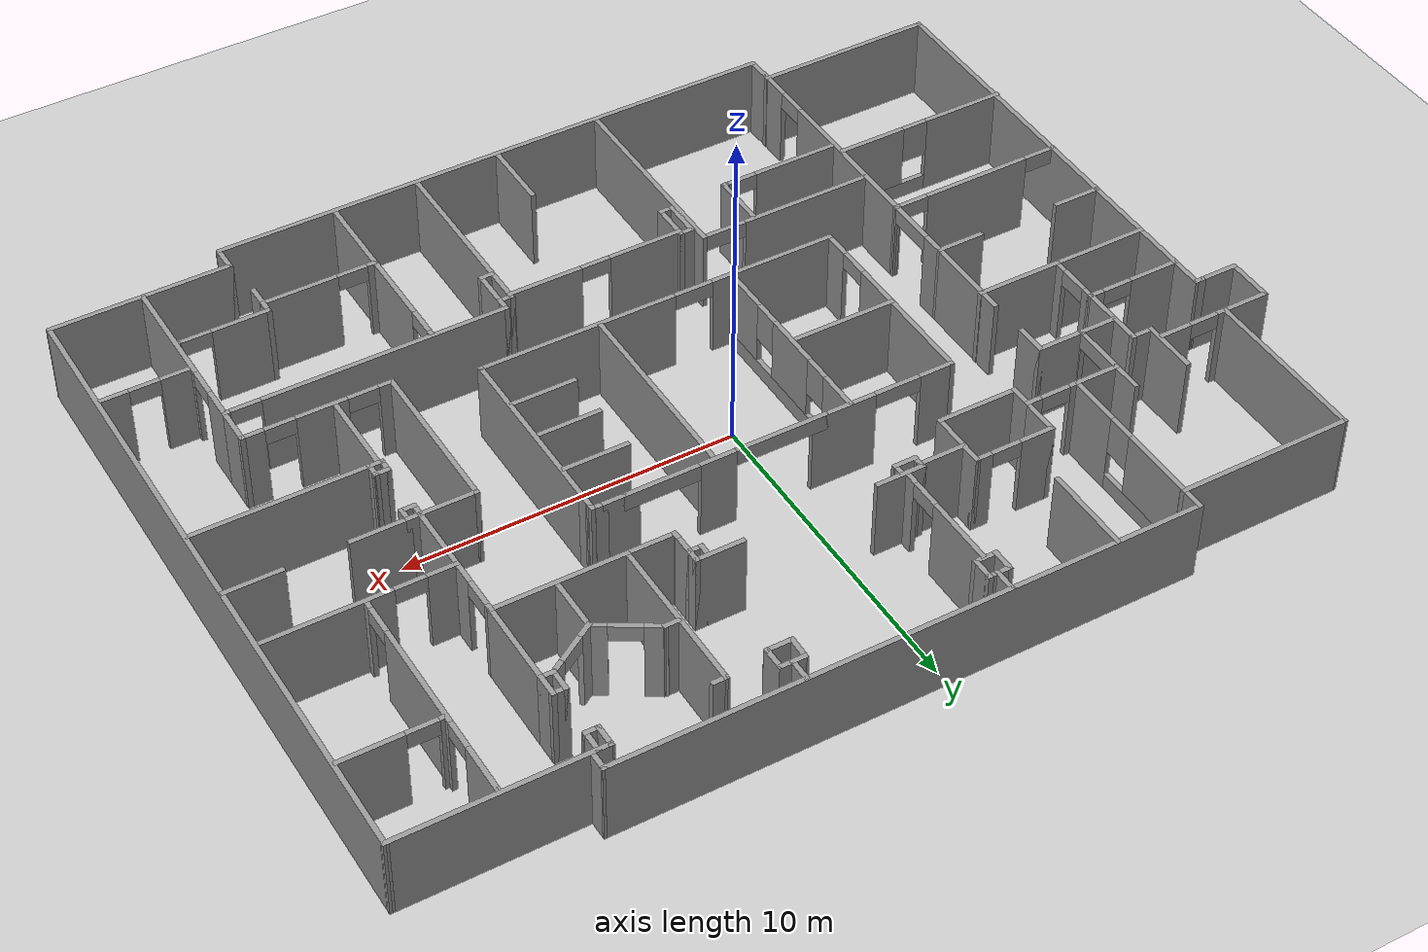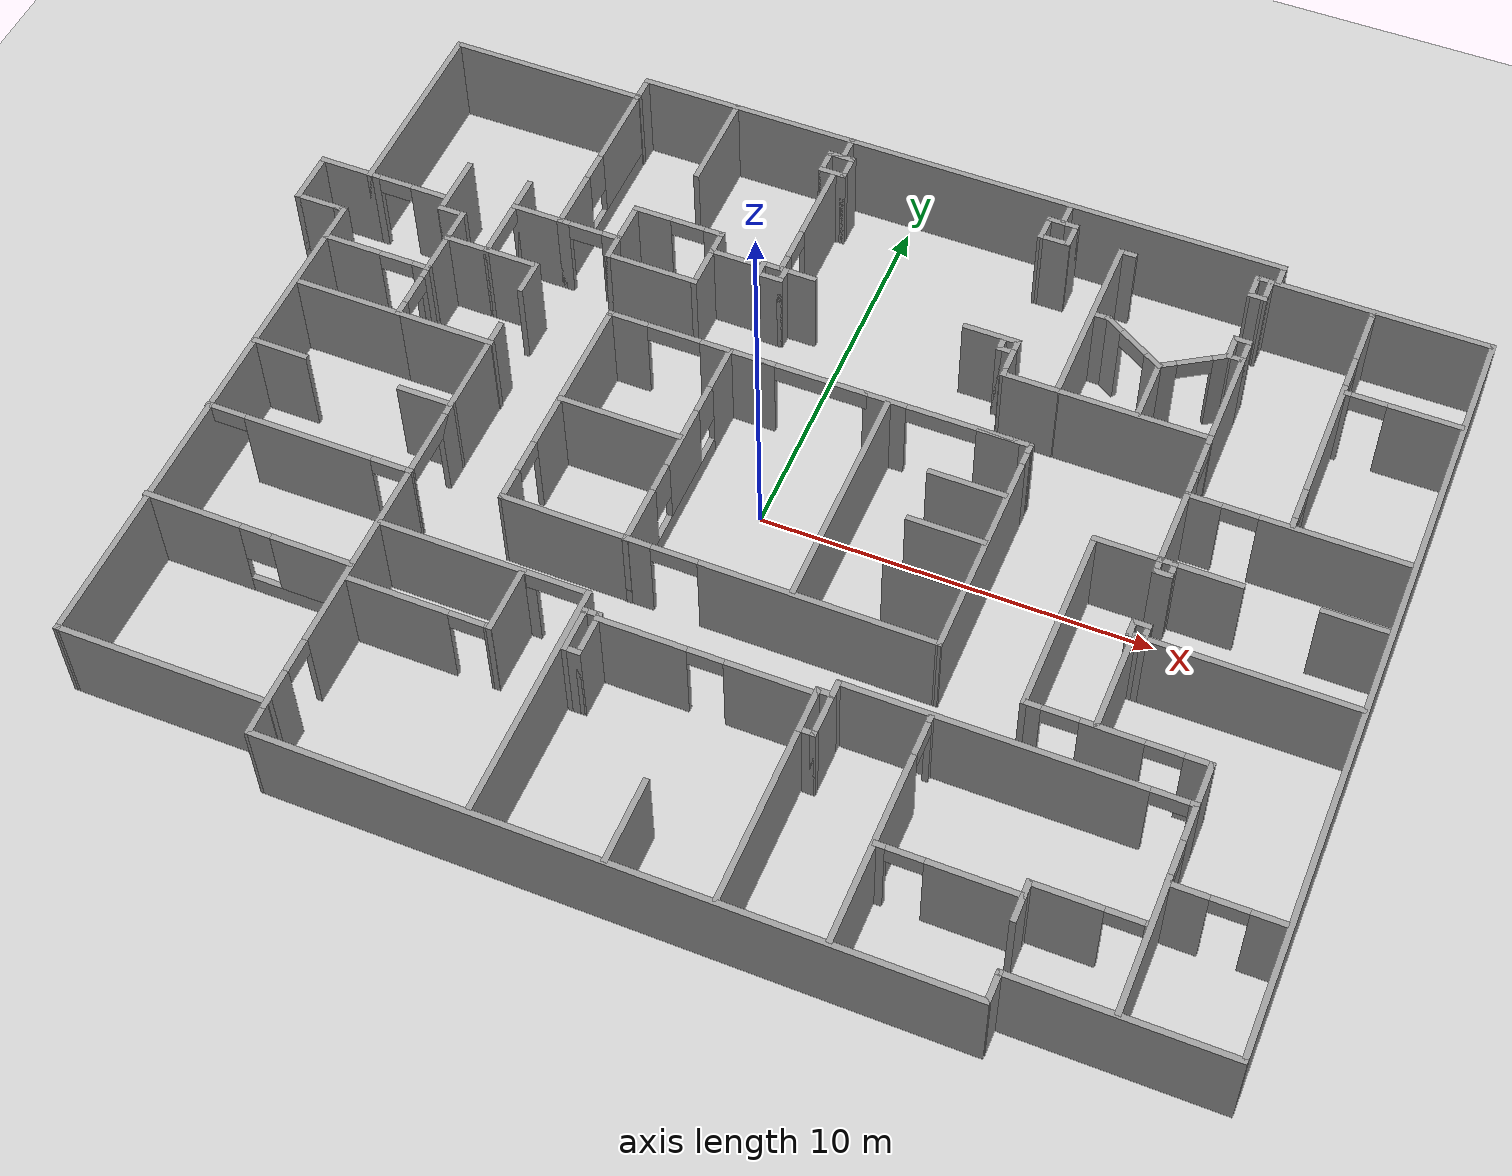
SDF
<sdf version="1.6">
 <world name="default">
  <light name="sun" type="directional">
   <pose>0 0 10 0 -0 0</pose>
   <diffuse>0.8 0.8 0.8 1</diffuse>
   <specular>0.2 0.2 0.2 1</specular>
   <attenuation>
    <range>1000</range>
    <constant>0.9</constant>
    <linear>0.01</linear>
    <quadratic>0.001</quadratic>
   </attenuation>
   <direction>-0.5 0.1 -0.9</direction>
  </light>
  <model name="ground_plane">
   <static>1</static>
   <link name="link">
    <collision name="collision">
     <geometry><plane><normal>0 0 1</normal><size>100 100</size></plane></geometry>
     <surface><friction><ode><mu>100</mu><mu2>50</mu2></ode></friction></surface>
    </collision>
    <visual name="visual">
     <cast_shadows>0</cast_shadows>
     <geometry><plane><normal>0 0 1</normal><size>100 100</size></plane></geometry>
     <material>
      <script><uri>file://media/materials/scripts/gazebo.material</uri><name>Gazebo/Grey</name></script>
     </material>
    </visual>
   </link>
  </model>
  <gravity>0 0 -9.8</gravity>
  <magnetic_field>6e-06 2.3e-05 -4.2e-05</magnetic_field>
  <atmosphere type="adiabatic"/>
  <physics name="default_physics" default="0" type="ode">
   <max_step_size>0.01</max_step_size>
   <real_time_factor>1</real_time_factor>
   <real_time_update_rate>100</real_time_update_rate>
  </physics>
  <scene><ambient>0.4 0.4 0.4 1</ambient><background>0.7 0.7 0.7 1</background><shadows>1</shadows></scene>
  <spherical_coordinates>
   <surface_model>EARTH_WGS84</surface_model>
   <latitude_deg>0</latitude_deg>
   <longitude_deg>0</longitude_deg>
   <elevation>0</elevation>
   <heading_deg>0</heading_deg>
  </spherical_coordinates>
  <model name="office02">
   <pose>0.554622 -0.475021 0 0 -0 0</pose>
   <link name="Wall_0">
    <collision name="Wall_0_Collision">
     <geometry><box><size>5.25 0.15 2.5</size></box></geometry>
     <pose>0 0 1.25 0 -0 0</pose>
    </collision>
    <visual name="Wall_0_Visual">
     <pose>0 0 1.25 0 -0 0</pose>
     <geometry><box><size>5.25 0.15 2.5</size></box></geometry>
     <material>
      <script><uri>file://media/materials/scripts/gazebo.material</uri><name>Gazebo/Grey</name></script>
      <ambient>1 1 1 1</ambient>
     </material>
     <meta><layer>0</layer></meta>
    </visual>
    <pose>-13.3071 7.70371 0 0 -0 -1.5708</pose>
   </link>
   <link name="Wall_1">
    <collision name="Wall_1_Collision">
     <geometry><box><size>1.5 0.15 2.5</size></box></geometry>
     <pose>0 0 1.25 0 -0 0</pose>
    </collision>
    <visual name="Wall_1_Visual">
     <pose>0 0 1.25 0 -0 0</pose>
     <geometry><box><size>1.5 0.15 2.5</size></box></geometry>
     <material>
      <script><uri>file://media/materials/scripts/gazebo.material</uri><name>Gazebo/Grey</name></script>
      <ambient>1 1 1 1</ambient>
     </material>
     <meta><layer>0</layer></meta>
    </visual>
    <pose>-13.9821 5.15371 0 0 -0 3.14159</pose>
   </link>
   <link name="Wall_100">
    <collision name="Wall_100_Collision">
     <geometry><box><size>0.25 0.15 2.5</size></box></geometry>
     <pose>0 0 1.25 0 -0 0</pose>
    </collision>
    <visual name="Wall_100_Visual">
     <pose>0 0 1.25 0 -0 0</pose>
     <geometry><box><size>0.25 0.15 2.5</size></box></geometry>
     <material>
      <script><uri>file://media/materials/scripts/gazebo.material</uri><name>Gazebo/Grey</name></script>
      <ambient>1 1 1 1</ambient>
     </material>
     <meta><layer>0</layer></meta>
    </visual>
    <pose>-2.1626 -5.16238 0 0 -0 -1.5708</pose>
   </link>
   <link name="Wall_101">
    <pose>0.512397 -5.21238 0 0 -0 0</pose>
    <visual name="Wall_101_Visual_0">
     <pose>-1.60035 0 1.25 0 -0 0</pose>
     <geometry><box><size>2.29931 0.15 2.5</size></box></geometry>
     <material>
      <script><uri>file://media/materials/scripts/gazebo.material</uri><name>Gazebo/Grey</name></script>
      <ambient>1 1 1 1</ambient>
     </material>
     <meta><layer>0</layer></meta>
    </visual>
    <collision name="Wall_101_Collision_0">
     <geometry><box><size>2.29931 0.15 2.5</size></box></geometry>
     <pose>-1.60035 0 1.25 0 -0 0</pose>
    </collision>
    <visual name="Wall_101_Visual_1">
     <pose>1.59965 0 1.25 0 -0 0</pose>
     <geometry><box><size>2.30069 0.15 2.5</size></box></geometry>
     <material>
      <script><uri>file://media/materials/scripts/gazebo.material</uri><name>Gazebo/Grey</name></script>
      <ambient>1 1 1 1</ambient>
     </material>
     <meta><layer>0</layer></meta>
    </visual>
    <collision name="Wall_101_Collision_1">
     <geometry><box><size>2.30069 0.15 2.5</size></box></geometry>
     <pose>1.59965 0 1.25 0 -0 0</pose>
    </collision>
    <visual name="Wall_101_Visual_2">
     <pose>-0.000692 0 2.25 0 -0 0</pose>
     <geometry><box><size>0.9 0.15 0.5</size></box></geometry>
     <material>
      <script><uri>file://media/materials/scripts/gazebo.material</uri><name>Gazebo/Grey</name></script>
      <ambient>1 1 1 1</ambient>
     </material>
     <meta><layer>0</layer></meta>
    </visual>
    <collision name="Wall_101_Collision_2">
     <geometry><box><size>0.9 0.15 0.5</size></box></geometry>
     <pose>-0.000692 0 2.25 0 -0 0</pose>
    </collision>
   </link>
   <link name="Wall_102">
    <collision name="Wall_102_Collision">
     <geometry><box><size>0.25 0.15 2.5</size></box></geometry>
     <pose>0 0 1.25 0 -0 0</pose>
    </collision>
    <visual name="Wall_102_Visual">
     <pose>0 0 1.25 0 -0 0</pose>
     <geometry><box><size>0.25 0.15 2.5</size></box></geometry>
     <material>
      <script><uri>file://media/materials/scripts/gazebo.material</uri><name>Gazebo/Grey</name></script>
      <ambient>1 1 1 1</ambient>
     </material>
     <meta><layer>0</layer></meta>
    </visual>
    <pose>3.1874 -5.16238 0 0 -0 1.5708</pose>
   </link>
   <link name="Wall_107">
    <collision name="Wall_107_Collision">
     <geometry><box><size>1.25 0.15 2.5</size></box></geometry>
     <pose>0 0 1.25 0 -0 0</pose>
    </collision>
    <visual name="Wall_107_Visual">
     <pose>0 0 1.25 0 -0 0</pose>
     <geometry><box><size>1.25 0.15 2.5</size></box></geometry>
     <material>
      <script><uri>file://media/materials/scripts/gazebo.material</uri><name>Gazebo/Grey</name></script>
      <ambient>1 1 1 1</ambient>
     </material>
     <meta><layer>0</layer></meta>
    </visual>
    <pose>3.1874 -5.66238 0 0 -0 -1.5708</pose>
   </link>
   <link name="Wall_115">
    <collision name="Wall_115_Collision">
     <geometry><box><size>0.5 0.15 2.5</size></box></geometry>
     <pose>0 0 1.25 0 -0 0</pose>
    </collision>
    <visual name="Wall_115_Visual">
     <pose>0 0 1.25 0 -0 0</pose>
     <geometry><box><size>0.5 0.15 2.5</size></box></geometry>
     <material>
      <script><uri>file://media/materials/scripts/gazebo.material</uri><name>Gazebo/Grey</name></script>
      <ambient>1 1 1 1</ambient>
     </material>
     <meta><layer>0</layer></meta>
    </visual>
    <pose>3.3624 -5.11238 0 0 -0 0</pose>
   </link>
   <link name="Wall_116">
    <collision name="Wall_116_Collision">
     <geometry><box><size>1.25 0.15 2.5</size></box></geometry>
     <pose>0 0 1.25 0 -0 0</pose>
    </collision>
    <visual name="Wall_116_Visual">
     <pose>0 0 1.25 0 -0 0</pose>
     <geometry><box><size>1.25 0.15 2.5</size></box></geometry>
     <material>
      <script><uri>file://media/materials/scripts/gazebo.material</uri><name>Gazebo/Grey</name></script>
      <ambient>1 1 1 1</ambient>
     </material>
     <meta><layer>0</layer></meta>
    </visual>
    <pose>3.5374 -5.66238 0 0 -0 -1.5708</pose>
   </link>
   <link name="Wall_117">
    <collision name="Wall_117_Collision">
     <geometry><box><size>0.5 0.15 2.5</size></box></geometry>
     <pose>0 0 1.25 0 -0 0</pose>
    </collision>
    <visual name="Wall_117_Visual">
     <pose>0 0 1.25 0 -0 0</pose>
     <geometry><box><size>0.5 0.15 2.5</size></box></geometry>
     <material>
      <script><uri>file://media/materials/scripts/gazebo.material</uri><name>Gazebo/Grey</name></script>
      <ambient>1 1 1 1</ambient>
     </material>
     <meta><layer>0</layer></meta>
    </visual>
    <pose>3.3624 -6.21238 0 0 -0 3.14159</pose>
   </link>
   <link name="Wall_119">
    <collision name="Wall_119_Collision">
     <geometry><box><size>4.75 0.15 2.5</size></box></geometry>
     <pose>0 0 1.25 0 -0 0</pose>
    </collision>
    <visual name="Wall_119_Visual">
     <pose>0 0 1.25 0 -0 0</pose>
     <geometry><box><size>4.75 0.15 2.5</size></box></geometry>
     <material>
      <script><uri>file://media/materials/scripts/gazebo.material</uri><name>Gazebo/Grey</name></script>
      <ambient>1 1 1 1</ambient>
     </material>
     <meta><layer>0</layer></meta>
    </visual>
    <pose>3.1874 -8.51238 0 0 -0 -1.5708</pose>
   </link>
   <link name="Wall_126">
    <collision name="Wall_126_Collision">
     <geometry><box><size>2.25 0.15 2.5</size></box></geometry>
     <pose>0 0 1.25 0 -0 0</pose>
    </collision>
    <visual name="Wall_126_Visual">
     <pose>0 0 1.25 0 -0 0</pose>
     <geometry><box><size>2.25 0.15 2.5</size></box></geometry>
     <material>
      <script><uri>file://media/materials/scripts/gazebo.material</uri><name>Gazebo/Grey</name></script>
      <ambient>1 1 1 1</ambient>
     </material>
     <meta><layer>0</layer></meta>
    </visual>
    <pose>0.607037 -9.77742 0 0 -0 -1.5708</pose>
   </link>
   <link name="Wall_128">
    <collision name="Wall_128_Collision">
     <geometry><box><size>0.5 0.15 2.5</size></box></geometry>
     <pose>0 0 1.25 0 -0 0</pose>
    </collision>
    <visual name="Wall_128_Visual">
     <pose>0 0 1.25 0 -0 0</pose>
     <geometry><box><size>0.5 0.15 2.5</size></box></geometry>
     <material>
      <script><uri>file://media/materials/scripts/gazebo.material</uri><name>Gazebo/Grey</name></script>
      <ambient>1 1 1 1</ambient>
     </material>
     <meta><layer>0</layer></meta>
    </visual>
    <pose>3.5374 -4.93738 0 0 -0 1.5708</pose>
   </link>
   <link name="Wall_129">
    <pose>7.7124 -4.76238 0 0 -0 0</pose>
    <visual name="Wall_129_Visual_0">
     <pose>-0.562587 0 1.25 0 -0 0</pose>
     <geometry><box><size>7.37483 0.15 2.5</size></box></geometry>
     <material>
      <script><uri>file://media/materials/scripts/gazebo.material</uri><name>Gazebo/Grey</name></script>
      <ambient>1 1 1 1</ambient>
     </material>
     <meta><layer>0</layer></meta>
    </visual>
    <collision name="Wall_129_Collision_0">
     <geometry><box><size>7.37483 0.15 2.5</size></box></geometry>
     <pose>-0.562587 0 1.25 0 -0 0</pose>
    </collision>
    <visual name="Wall_129_Visual_1">
     <pose>4.13741 0 1.25 0 -0 0</pose>
     <geometry><box><size>0.225175 0.15 2.5</size></box></geometry>
     <material>
      <script><uri>file://media/materials/scripts/gazebo.material</uri><name>Gazebo/Grey</name></script>
      <ambient>1 1 1 1</ambient>
     </material>
     <meta><layer>0</layer></meta>
    </visual>
    <collision name="Wall_129_Collision_1">
     <geometry><box><size>0.225175 0.15 2.5</size></box></geometry>
     <pose>4.13741 0 1.25 0 -0 0</pose>
    </collision>
    <visual name="Wall_129_Visual_2">
     <pose>3.57483 0 2.25 0 -0 0</pose>
     <geometry><box><size>0.9 0.15 0.5</size></box></geometry>
     <material>
      <script><uri>file://media/materials/scripts/gazebo.material</uri><name>Gazebo/Grey</name></script>
      <ambient>1 1 1 1</ambient>
     </material>
     <meta><layer>0</layer></meta>
    </visual>
    <collision name="Wall_129_Collision_2">
     <geometry><box><size>0.9 0.15 0.5</size></box></geometry>
     <pose>3.57483 0 2.25 0 -0 0</pose>
    </collision>
   </link>
   <link name="Wall_131">
    <pose>11.8874 -7.43738 0 0 -0 -1.5708</pose>
    <visual name="Wall_131_Visual_0">
     <pose>-2.23917 0 1.25 0 -0 0</pose>
     <geometry><box><size>1.02166 0.15 2.5</size></box></geometry>
     <material>
      <script><uri>file://media/materials/scripts/gazebo.material</uri><name>Gazebo/Grey</name></script>
      <ambient>1 1 1 1</ambient>
     </material>
     <meta><layer>0</layer></meta>
    </visual>
    <collision name="Wall_131_Collision_0">
     <geometry><box><size>1.02166 0.15 2.5</size></box></geometry>
     <pose>-2.23917 0 1.25 0 -0 0</pose>
    </collision>
    <visual name="Wall_131_Visual_1">
     <pose>0.960831 0 1.25 0 -0 0</pose>
     <geometry><box><size>3.57834 0.15 2.5</size></box></geometry>
     <material>
      <script><uri>file://media/materials/scripts/gazebo.material</uri><name>Gazebo/Grey</name></script>
      <ambient>1 1 1 1</ambient>
     </material>
     <meta><layer>0</layer></meta>
    </visual>
    <collision name="Wall_131_Collision_1">
     <geometry><box><size>3.57834 0.15 2.5</size></box></geometry>
     <pose>0.960831 0 1.25 0 -0 0</pose>
    </collision>
    <visual name="Wall_131_Visual_2">
     <pose>-1.27834 0 2.25 0 -0 0</pose>
     <geometry><box><size>0.9 0.15 0.5</size></box></geometry>
     <material>
      <script><uri>file://media/materials/scripts/gazebo.material</uri><name>Gazebo/Grey</name></script>
      <ambient>1 1 1 1</ambient>
     </material>
     <meta><layer>0</layer></meta>
    </visual>
    <collision name="Wall_131_Collision_2">
     <geometry><box><size>0.9 0.15 0.5</size></box></geometry>
     <pose>-1.27834 0 2.25 0 -0 0</pose>
    </collision>
   </link>
   <link name="Wall_133">
    <pose>5.7673 -7.82763 0 0 -0 -1.5708</pose>
    <visual name="Wall_133_Visual_0">
     <pose>-2.95016 0 1.25 0 -0 0</pose>
     <geometry><box><size>0.19969 0.15 2.5</size></box></geometry>
     <material>
      <script><uri>file://media/materials/scripts/gazebo.material</uri><name>Gazebo/Grey</name></script>
      <ambient>1 1 1 1</ambient>
     </material>
     <meta><layer>0</layer></meta>
    </visual>
    <collision name="Wall_133_Collision_0">
     <geometry><box><size>0.19969 0.15 2.5</size></box></geometry>
     <pose>-2.95016 0 1.25 0 -0 0</pose>
    </collision>
    <visual name="Wall_133_Visual_1">
     <pose>0.549845 0 1.25 0 -0 0</pose>
     <geometry><box><size>5.00031 0.15 2.5</size></box></geometry>
     <material>
      <script><uri>file://media/materials/scripts/gazebo.material</uri><name>Gazebo/Grey</name></script>
      <ambient>1 1 1 1</ambient>
     </material>
     <meta><layer>0</layer></meta>
    </visual>
    <collision name="Wall_133_Collision_1">
     <geometry><box><size>5.00031 0.15 2.5</size></box></geometry>
     <pose>0.549845 0 1.25 0 -0 0</pose>
    </collision>
    <visual name="Wall_133_Visual_2">
     <pose>-2.40031 0 2.25 0 -0 0</pose>
     <geometry><box><size>0.9 0.15 0.5</size></box></geometry>
     <material>
      <script><uri>file://media/materials/scripts/gazebo.material</uri><name>Gazebo/Grey</name></script>
      <ambient>1 1 1 1</ambient>
     </material>
     <meta><layer>0</layer></meta>
    </visual>
    <collision name="Wall_133_Collision_2">
     <geometry><box><size>0.9 0.15 0.5</size></box></geometry>
     <pose>-2.40031 0 2.25 0 -0 0</pose>
    </collision>
   </link>
   <link name="Wall_135">
    <pose>7.48822 -8.27933 0 0 -0 0</pose>
    <visual name="Wall_135_Visual_0">
     <pose>-1.604 0 1.25 0 -0 0</pose>
     <geometry><box><size>0.292 0.15 2.5</size></box></geometry>
     <material>
      <script><uri>file://media/materials/scripts/gazebo.material</uri><name>Gazebo/Grey</name></script>
      <ambient>1 1 1 1</ambient>
     </material>
     <meta><layer>0</layer></meta>
    </visual>
    <collision name="Wall_135_Collision_0">
     <geometry><box><size>0.292 0.15 2.5</size></box></geometry>
     <pose>-1.604 0 1.25 0 -0 0</pose>
    </collision>
    <visual name="Wall_135_Visual_1">
     <pose>0.596 0 1.25 0 -0 0</pose>
     <geometry><box><size>2.308 0.15 2.5</size></box></geometry>
     <material>
      <script><uri>file://media/materials/scripts/gazebo.material</uri><name>Gazebo/Grey</name></script>
      <ambient>1 1 1 1</ambient>
     </material>
     <meta><layer>0</layer></meta>
    </visual>
    <collision name="Wall_135_Collision_1">
     <geometry><box><size>2.308 0.15 2.5</size></box></geometry>
     <pose>0.596 0 1.25 0 -0 0</pose>
    </collision>
    <visual name="Wall_135_Visual_2">
     <pose>-1.008 0 2.25 0 -0 0</pose>
     <geometry><box><size>0.9 0.15 0.5</size></box></geometry>
     <material>
      <script><uri>file://media/materials/scripts/gazebo.material</uri><name>Gazebo/Grey</name></script>
      <ambient>1 1 1 1</ambient>
     </material>
     <meta><layer>0</layer></meta>
    </visual>
    <collision name="Wall_135_Collision_2">
     <geometry><box><size>0.9 0.15 0.5</size></box></geometry>
     <pose>-1.008 0 2.25 0 -0 0</pose>
    </collision>
   </link>
   <link name="Wall_136">
    <collision name="Wall_136_Collision">
     <geometry><box><size>0.5 0.15 2.5</size></box></geometry>
     <pose>0 0 1.25 0 -0 0</pose>
    </collision>
    <visual name="Wall_136_Visual">
     <pose>0 0 1.25 0 -0 0</pose>
     <geometry><box><size>0.5 0.15 2.5</size></box></geometry>
     <material>
      <script><uri>file://media/materials/scripts/gazebo.material</uri><name>Gazebo/Grey</name></script>
      <ambient>1 1 1 1</ambient>
     </material>
     <meta><layer>0</layer></meta>
    </visual>
    <pose>9.16322 -8.10432 0 0 -0 1.5708</pose>
   </link>
   <link name="Wall_137">
    <pose>10.4632 -7.92933 0 0 -0 0</pose>
    <visual name="Wall_137_Visual_0">
     <pose>-0.489 0 1.25 0 -0 0</pose>
     <geometry><box><size>1.772 0.15 2.5</size></box></geometry>
     <material>
      <script><uri>file://media/materials/scripts/gazebo.material</uri><name>Gazebo/Grey</name></script>
      <ambient>1 1 1 1</ambient>
     </material>
     <meta><layer>0</layer></meta>
    </visual>
    <collision name="Wall_137_Collision_0">
     <geometry><box><size>1.772 0.15 2.5</size></box></geometry>
     <pose>-0.489 0 1.25 0 -0 0</pose>
    </collision>
    <visual name="Wall_137_Visual_1">
     <pose>1.336 0 1.25 0 -0 0</pose>
     <geometry><box><size>0.078 0.15 2.5</size></box></geometry>
     <material>
      <script><uri>file://media/materials/scripts/gazebo.material</uri><name>Gazebo/Grey</name></script>
      <ambient>1 1 1 1</ambient>
     </material>
     <meta><layer>0</layer></meta>
    </visual>
    <collision name="Wall_137_Collision_1">
     <geometry><box><size>0.078 0.15 2.5</size></box></geometry>
     <pose>1.336 0 1.25 0 -0 0</pose>
    </collision>
    <visual name="Wall_137_Visual_2">
     <pose>0.847 0 2.25 0 -0 0</pose>
     <geometry><box><size>0.9 0.15 0.5</size></box></geometry>
     <material>
      <script><uri>file://media/materials/scripts/gazebo.material</uri><name>Gazebo/Grey</name></script>
      <ambient>1 1 1 1</ambient>
     </material>
     <meta><layer>0</layer></meta>
    </visual>
    <collision name="Wall_137_Collision_2">
     <geometry><box><size>0.9 0.15 0.5</size></box></geometry>
     <pose>0.847 0 2.25 0 -0 0</pose>
    </collision>
   </link>
   <link name="Wall_139">
    <collision name="Wall_139_Collision">
     <geometry><box><size>0.75 0.15 2.5</size></box></geometry>
     <pose>0 0 1.25 0 -0 0</pose>
    </collision>
    <visual name="Wall_139_Visual">
     <pose>0 0 1.25 0 -0 0</pose>
     <geometry><box><size>0.75 0.15 2.5</size></box></geometry>
     <material>
      <script><uri>file://media/materials/scripts/gazebo.material</uri><name>Gazebo/Grey</name></script>
      <ambient>1 1 1 1</ambient>
     </material>
     <meta><layer>0</layer></meta>
    </visual>
    <pose>9.16322 -8.57933 0 0 -0 -1.5708</pose>
   </link>
   <link name="Wall_141">
    <pose>13.1852 -6.83033 0 0 -0 0</pose>
    <visual name="Wall_141_Visual_0">
     <pose>-0.865994 0 1.25 0 -0 0</pose>
     <geometry><box><size>1.01801 0.15 2.5</size></box></geometry>
     <material>
      <script><uri>file://media/materials/scripts/gazebo.material</uri><name>Gazebo/Grey</name></script>
      <ambient>1 1 1 1</ambient>
     </material>
     <meta><layer>0</layer></meta>
    </visual>
    <collision name="Wall_141_Collision_0">
     <geometry><box><size>1.01801 0.15 2.5</size></box></geometry>
     <pose>-0.865994 0 1.25 0 -0 0</pose>
    </collision>
    <visual name="Wall_141_Visual_1">
     <pose>0.959006 0 1.25 0 -0 0</pose>
     <geometry><box><size>0.831988 0.15 2.5</size></box></geometry>
     <material>
      <script><uri>file://media/materials/scripts/gazebo.material</uri><name>Gazebo/Grey</name></script>
      <ambient>1 1 1 1</ambient>
     </material>
     <meta><layer>0</layer></meta>
    </visual>
    <collision name="Wall_141_Collision_1">
     <geometry><box><size>0.831988 0.15 2.5</size></box></geometry>
     <pose>0.959006 0 1.25 0 -0 0</pose>
    </collision>
    <visual name="Wall_141_Visual_2">
     <pose>0.093012 0 2.25 0 -0 0</pose>
     <geometry><box><size>0.9 0.15 0.5</size></box></geometry>
     <material>
      <script><uri>file://media/materials/scripts/gazebo.material</uri><name>Gazebo/Grey</name></script>
      <ambient>1 1 1 1</ambient>
     </material>
     <meta><layer>0</layer></meta>
    </visual>
    <collision name="Wall_141_Collision_2">
     <geometry><box><size>0.9 0.15 0.5</size></box></geometry>
     <pose>0.093012 0 2.25 0 -0 0</pose>
    </collision>
   </link>
   <link name="Wall_144">
    <collision name="Wall_144_Collision">
     <geometry><box><size>1.25 0.15 2.5</size></box></geometry>
     <pose>0 0 1.25 0 -0 0</pose>
    </collision>
    <visual name="Wall_144_Visual">
     <pose>0 0 1.25 0 -0 0</pose>
     <geometry><box><size>1.25 0.15 2.5</size></box></geometry>
     <material>
      <script><uri>file://media/materials/scripts/gazebo.material</uri><name>Gazebo/Grey</name></script>
      <ambient>1 1 1 1</ambient>
     </material>
     <meta><layer>0</layer></meta>
    </visual>
    <pose>11.8874 -4.21238 0 0 -0 1.5708</pose>
   </link>
   <link name="Wall_147">
    <pose>9.7124 -3.66238 0 0 -0 3.14159</pose>
    <visual name="Wall_147_Visual_0">
     <pose>-1.89817 0 1.25 0 -0 0</pose>
     <geometry><box><size>0.703666 0.15 2.5</size></box></geometry>
     <material>
      <script><uri>file://media/materials/scripts/gazebo.material</uri><name>Gazebo/Grey</name></script>
      <ambient>1 1 1 1</ambient>
     </material>
     <meta><layer>0</layer></meta>
    </visual>
    <collision name="Wall_147_Collision_0">
     <geometry><box><size>0.703666 0.15 2.5</size></box></geometry>
     <pose>-1.89817 0 1.25 0 -0 0</pose>
    </collision>
    <visual name="Wall_147_Visual_1">
     <pose>0.111166 0 1.25 0 -0 0</pose>
     <geometry><box><size>1.515 0.15 2.5</size></box></geometry>
     <material>
      <script><uri>file://media/materials/scripts/gazebo.material</uri><name>Gazebo/Grey</name></script>
      <ambient>1 1 1 1</ambient>
     </material>
     <meta><layer>0</layer></meta>
    </visual>
    <collision name="Wall_147_Collision_1">
     <geometry><box><size>1.515 0.15 2.5</size></box></geometry>
     <pose>0.111166 0 1.25 0 -0 0</pose>
    </collision>
    <visual name="Wall_147_Visual_2">
     <pose>2.00933 0 1.25 0 -0 0</pose>
     <geometry><box><size>0.481334 0.15 2.5</size></box></geometry>
     <material>
      <script><uri>file://media/materials/scripts/gazebo.material</uri><name>Gazebo/Grey</name></script>
      <ambient>1 1 1 1</ambient>
     </material>
     <meta><layer>0</layer></meta>
    </visual>
    <collision name="Wall_147_Collision_2">
     <geometry><box><size>0.481334 0.15 2.5</size></box></geometry>
     <pose>2.00933 0 1.25 0 -0 0</pose>
    </collision>
    <visual name="Wall_147_Visual_3">
     <pose>-1.09633 0 2.25 0 -0 0</pose>
     <geometry><box><size>0.9 0.15 0.5</size></box></geometry>
     <material>
      <script><uri>file://media/materials/scripts/gazebo.material</uri><name>Gazebo/Grey</name></script>
      <ambient>1 1 1 1</ambient>
     </material>
     <meta><layer>0</layer></meta>
    </visual>
    <collision name="Wall_147_Collision_3">
     <geometry><box><size>0.9 0.15 0.5</size></box></geometry>
     <pose>-1.09633 0 2.25 0 -0 0</pose>
    </collision>
    <visual name="Wall_147_Visual_4">
     <pose>1.31867 0 2.25 0 -0 0</pose>
     <geometry><box><size>0.9 0.15 0.5</size></box></geometry>
     <material>
      <script><uri>file://media/materials/scripts/gazebo.material</uri><name>Gazebo/Grey</name></script>
      <ambient>1 1 1 1</ambient>
     </material>
     <meta><layer>0</layer></meta>
    </visual>
    <collision name="Wall_147_Collision_4">
     <geometry><box><size>0.9 0.15 0.5</size></box></geometry>
     <pose>1.31867 0 2.25 0 -0 0</pose>
    </collision>
   </link>
   <link name="Wall_148">
    <collision name="Wall_148_Collision">
     <geometry><box><size>5 0.15 2.5</size></box></geometry>
     <pose>0 0 1.25 0 -0 0</pose>
    </collision>
    <visual name="Wall_148_Visual">
     <pose>0 0 1.25 0 -0 0</pose>
     <geometry><box><size>5 0.15 2.5</size></box></geometry>
     <material>
      <script><uri>file://media/materials/scripts/gazebo.material</uri><name>Gazebo/Grey</name></script>
      <ambient>1 1 1 1</ambient>
     </material>
     <meta><layer>0</layer></meta>
    </visual>
    <pose>7.5374 -1.23738 0 0 -0 1.5708</pose>
   </link>
   <link name="Wall_149">
    <collision name="Wall_149_Collision">
     <geometry><box><size>1.75 0.15 2.5</size></box></geometry>
     <pose>0 0 1.25 0 -0 0</pose>
    </collision>
    <visual name="Wall_149_Visual">
     <pose>0 0 1.25 0 -0 0</pose>
     <geometry><box><size>1.75 0.15 2.5</size></box></geometry>
     <material>
      <script><uri>file://media/materials/scripts/gazebo.material</uri><name>Gazebo/Grey</name></script>
      <ambient>1 1 1 1</ambient>
     </material>
     <meta><layer>0</layer></meta>
    </visual>
    <pose>8.3374 1.18762 0 0 -0 0</pose>
   </link>
   <link name="Wall_150">
    <pose>9.1374 3.11262 0 0 -0 1.5708</pose>
    <visual name="Wall_150_Visual_0">
     <pose>-0.589768 0 1.25 0 -0 0</pose>
     <geometry><box><size>2.82046 0.15 2.5</size></box></geometry>
     <material>
      <script><uri>file://media/materials/scripts/gazebo.material</uri><name>Gazebo/Grey</name></script>
      <ambient>1 1 1 1</ambient>
     </material>
     <meta><layer>0</layer></meta>
    </visual>
    <collision name="Wall_150_Collision_0">
     <geometry><box><size>2.82046 0.15 2.5</size></box></geometry>
     <pose>-0.589768 0 1.25 0 -0 0</pose>
    </collision>
    <visual name="Wall_150_Visual_1">
     <pose>1.86023 0 1.25 0 -0 0</pose>
     <geometry><box><size>0.279535 0.15 2.5</size></box></geometry>
     <material>
      <script><uri>file://media/materials/scripts/gazebo.material</uri><name>Gazebo/Grey</name></script>
      <ambient>1 1 1 1</ambient>
     </material>
     <meta><layer>0</layer></meta>
    </visual>
    <collision name="Wall_150_Collision_1">
     <geometry><box><size>0.279535 0.15 2.5</size></box></geometry>
     <pose>1.86023 0 1.25 0 -0 0</pose>
    </collision>
    <visual name="Wall_150_Visual_2">
     <pose>1.27046 0 2.25 0 -0 0</pose>
     <geometry><box><size>0.9 0.15 0.5</size></box></geometry>
     <material>
      <script><uri>file://media/materials/scripts/gazebo.material</uri><name>Gazebo/Grey</name></script>
      <ambient>1 1 1 1</ambient>
     </material>
     <meta><layer>0</layer></meta>
    </visual>
    <collision name="Wall_150_Collision_2">
     <geometry><box><size>0.9 0.15 0.5</size></box></geometry>
     <pose>1.27046 0 2.25 0 -0 0</pose>
    </collision>
   </link>
   <link name="Wall_151">
    <collision name="Wall_151_Collision">
     <geometry><box><size>4 0.15 2.5</size></box></geometry>
     <pose>0 0 1.25 0 -0 0</pose>
    </collision>
    <visual name="Wall_151_Visual">
     <pose>0 0 1.25 0 -0 0</pose>
     <geometry><box><size>4 0.15 2.5</size></box></geometry>
     <material>
      <script><uri>file://media/materials/scripts/gazebo.material</uri><name>Gazebo/Grey</name></script>
      <ambient>1 1 1 1</ambient>
     </material>
     <meta><layer>0</layer></meta>
    </visual>
    <pose>7.2124 5.03762 0 0 -0 3.14159</pose>
   </link>
   <link name="Wall_153">
    <collision name="Wall_153_Collision">
     <geometry><box><size>5 0.15 2.5</size></box></geometry>
     <pose>0 0 1.25 0 -0 0</pose>
    </collision>
    <visual name="Wall_153_Visual">
     <pose>0 0 1.25 0 -0 0</pose>
     <geometry><box><size>5 0.15 2.5</size></box></geometry>
     <material>
      <script><uri>file://media/materials/scripts/gazebo.material</uri><name>Gazebo/Grey</name></script>
      <ambient>1 1 1 1</ambient>
     </material>
     <meta><layer>0</layer></meta>
    </visual>
    <pose>5.2874 7.46262 0 0 -0 1.5708</pose>
   </link>
   <link name="Wall_154">
    <collision name="Wall_154_Collision">
     <geometry><box><size>0.5 0.15 2.5</size></box></geometry>
     <pose>0 0 1.25 0 -0 0</pose>
    </collision>
    <visual name="Wall_154_Visual">
     <pose>0 0 1.25 0 -0 0</pose>
     <geometry><box><size>0.5 0.15 2.5</size></box></geometry>
     <material>
      <script><uri>file://media/materials/scripts/gazebo.material</uri><name>Gazebo/Grey</name></script>
      <ambient>1 1 1 1</ambient>
     </material>
     <meta><layer>0</layer></meta>
    </visual>
    <pose>5.46235 9.88749 0 0 -0 -0.000714</pose>
   </link>
   <link name="Wall_160">
    <collision name="Wall_160_Collision">
     <geometry><box><size>2.75 0.15 2.5</size></box></geometry>
     <pose>0 0 1.25 0 -0 0</pose>
    </collision>
    <visual name="Wall_160_Visual">
     <pose>0 0 1.25 0 -0 0</pose>
     <geometry><box><size>2.75 0.15 2.5</size></box></geometry>
     <material>
      <script><uri>file://media/materials/scripts/gazebo.material</uri><name>Gazebo/Grey</name></script>
      <ambient>1 1 1 1</ambient>
     </material>
     <meta><layer>0</layer></meta>
    </visual>
    <pose>9.22173 -2.33855 0 0 -0 -1.5708</pose>
   </link>
   <link name="Wall_162">
    <collision name="Wall_162_Collision">
     <geometry><box><size>5.5 0.15 2.5</size></box></geometry>
     <pose>0 0 1.25 0 -0 0</pose>
    </collision>
    <visual name="Wall_162_Visual">
     <pose>0 0 1.25 0 -0 0</pose>
     <geometry><box><size>5.5 0.15 2.5</size></box></geometry>
     <material>
      <script><uri>file://media/materials/scripts/gazebo.material</uri><name>Gazebo/Grey</name></script>
      <ambient>1 1 1 1</ambient>
     </material>
     <meta><layer>0</layer></meta>
    </visual>
    <pose>11.8967 -1.03855 0 0 -0 0</pose>
   </link>
   <link name="Wall_169">
    <collision name="Wall_169_Collision">
     <geometry><box><size>0.5 0.15 2.5</size></box></geometry>
     <pose>0 0 1.25 0 -0 0</pose>
    </collision>
    <visual name="Wall_169_Visual">
     <pose>0 0 1.25 0 -0 0</pose>
     <geometry><box><size>0.5 0.15 2.5</size></box></geometry>
     <material>
      <script><uri>file://media/materials/scripts/gazebo.material</uri><name>Gazebo/Grey</name></script>
      <ambient>1 1 1 1</ambient>
     </material>
     <meta><layer>0</layer></meta>
    </visual>
    <pose>9.3124 1.18762 0 0 -0 0</pose>
   </link>
   <link name="Wall_17">
    <collision name="Wall_17_Collision">
     <geometry><box><size>20.5768 0.15 2.5</size></box></geometry>
     <pose>0 0 1.25 0 -0 0</pose>
    </collision>
    <visual name="Wall_17_Visual">
     <pose>0 0 1.25 0 -0 0</pose>
     <geometry><box><size>20.5768 0.15 2.5</size></box></geometry>
     <material>
      <script><uri>file://media/materials/scripts/gazebo.material</uri><name>Gazebo/Grey</name></script>
      <ambient>1 1 1 1</ambient>
     </material>
     <meta><layer>0</layer></meta>
    </visual>
    <pose>14.634 0.128909 0 0 -0 1.56854</pose>
   </link>
   <link name="Wall_170">
    <collision name="Wall_170_Collision">
     <geometry><box><size>0.5 0.15 2.5</size></box></geometry>
     <pose>0 0 1.25 0 -0 0</pose>
    </collision>
    <visual name="Wall_170_Visual">
     <pose>0 0 1.25 0 -0 0</pose>
     <geometry><box><size>0.5 0.15 2.5</size></box></geometry>
     <material>
      <script><uri>file://media/materials/scripts/gazebo.material</uri><name>Gazebo/Grey</name></script>
      <ambient>1 1 1 1</ambient>
     </material>
     <meta><layer>0</layer></meta>
    </visual>
    <pose>9.4874 1.01262 0 0 -0 -1.5708</pose>
   </link>
   <link name="Wall_171">
    <collision name="Wall_171_Collision">
     <geometry><box><size>0.5 0.15 2.5</size></box></geometry>
     <pose>0 0 1.25 0 -0 0</pose>
    </collision>
    <visual name="Wall_171_Visual">
     <pose>0 0 1.25 0 -0 0</pose>
     <geometry><box><size>0.5 0.15 2.5</size></box></geometry>
     <material>
      <script><uri>file://media/materials/scripts/gazebo.material</uri><name>Gazebo/Grey</name></script>
      <ambient>1 1 1 1</ambient>
     </material>
     <meta><layer>0</layer></meta>
    </visual>
    <pose>9.3124 0.837616 0 0 -0 3.14159</pose>
   </link>
   <link name="Wall_172">
    <collision name="Wall_172_Collision">
     <geometry><box><size>0.5 0.15 2.5</size></box></geometry>
     <pose>0 0 1.25 0 -0 0</pose>
    </collision>
    <visual name="Wall_172_Visual">
     <pose>0 0 1.25 0 -0 0</pose>
     <geometry><box><size>0.5 0.15 2.5</size></box></geometry>
     <material>
      <script><uri>file://media/materials/scripts/gazebo.material</uri><name>Gazebo/Grey</name></script>
      <ambient>1 1 1 1</ambient>
     </material>
     <meta><layer>0</layer></meta>
    </visual>
    <pose>9.1374 1.01262 0 0 -0 1.5708</pose>
   </link>
   <link name="Wall_174">
    <collision name="Wall_174_Collision">
     <geometry><box><size>0.25 0.15 2.5</size></box></geometry>
     <pose>0 0 1.25 0 -0 0</pose>
    </collision>
    <visual name="Wall_174_Visual">
     <pose>0 0 1.25 0 -0 0</pose>
     <geometry><box><size>0.25 0.15 2.5</size></box></geometry>
     <material>
      <script><uri>file://media/materials/scripts/gazebo.material</uri><name>Gazebo/Grey</name></script>
      <ambient>1 1 1 1</ambient>
     </material>
     <meta><layer>0</layer></meta>
    </visual>
    <pose>9.17173 -1.03855 0 0 -0 3.14159</pose>
   </link>
   <link name="Wall_175">
    <collision name="Wall_175_Collision">
     <geometry><box><size>0.5 0.15 2.5</size></box></geometry>
     <pose>0 0 1.25 0 -0 0</pose>
    </collision>
    <visual name="Wall_175_Visual">
     <pose>0 0 1.25 0 -0 0</pose>
     <geometry><box><size>0.5 0.15 2.5</size></box></geometry>
     <material>
      <script><uri>file://media/materials/scripts/gazebo.material</uri><name>Gazebo/Grey</name></script>
      <ambient>1 1 1 1</ambient>
     </material>
     <meta><layer>0</layer></meta>
    </visual>
    <pose>9.12173 -0.863553 0 0 -0 1.5708</pose>
   </link>
   <link name="Wall_176">
    <collision name="Wall_176_Collision">
     <geometry><box><size>0.5 0.15 2.5</size></box></geometry>
     <pose>0 0 1.25 0 -0 0</pose>
    </collision>
    <visual name="Wall_176_Visual">
     <pose>0 0 1.25 0 -0 0</pose>
     <geometry><box><size>0.5 0.15 2.5</size></box></geometry>
     <material>
      <script><uri>file://media/materials/scripts/gazebo.material</uri><name>Gazebo/Grey</name></script>
      <ambient>1 1 1 1</ambient>
     </material>
     <meta><layer>0</layer></meta>
    </visual>
    <pose>9.29673 -0.688553 0 0 -0 0</pose>
   </link>
   <link name="Wall_177">
    <collision name="Wall_177_Collision">
     <geometry><box><size>0.5 0.15 2.5</size></box></geometry>
     <pose>0 0 1.25 0 -0 0</pose>
    </collision>
    <visual name="Wall_177_Visual">
     <pose>0 0 1.25 0 -0 0</pose>
     <geometry><box><size>0.5 0.15 2.5</size></box></geometry>
     <material>
      <script><uri>file://media/materials/scripts/gazebo.material</uri><name>Gazebo/Grey</name></script>
      <ambient>1 1 1 1</ambient>
     </material>
     <meta><layer>0</layer></meta>
    </visual>
    <pose>9.47173 -0.863553 0 0 -0 -1.5708</pose>
   </link>
   <link name="Wall_179">
    <collision name="Wall_179_Collision">
     <geometry><box><size>1.75 0.15 2.5</size></box></geometry>
     <pose>0 0 1.25 0 -0 0</pose>
    </collision>
    <visual name="Wall_179_Visual">
     <pose>0 0 1.25 0 -0 0</pose>
     <geometry><box><size>1.75 0.15 2.5</size></box></geometry>
     <material>
      <script><uri>file://media/materials/scripts/gazebo.material</uri><name>Gazebo/Grey</name></script>
      <ambient>1 1 1 1</ambient>
     </material>
     <meta><layer>0</layer></meta>
    </visual>
    <pose>10.2874 1.18762 0 0 -0 0</pose>
   </link>
   <link name="Wall_181">
    <collision name="Wall_181_Collision">
     <geometry><box><size>1.75 0.15 2.5</size></box></geometry>
     <pose>0 0 1.25 0 -0 0</pose>
    </collision>
    <visual name="Wall_181_Visual">
     <pose>0 0 1.25 0 -0 0</pose>
     <geometry><box><size>1.75 0.15 2.5</size></box></geometry>
     <material>
      <script><uri>file://media/materials/scripts/gazebo.material</uri><name>Gazebo/Grey</name></script>
      <ambient>1 1 1 1</ambient>
     </material>
     <meta><layer>0</layer></meta>
    </visual>
    <pose>13.8007 1.21968 0 0 -0 0</pose>
   </link>
   <link name="Wall_183">
    <pose>11.8204 3.21781 0 0 -0 0</pose>
    <visual name="Wall_183_Visual_0">
     <pose>-2.28982 0 1.25 0 -0 0</pose>
     <geometry><box><size>0.920353 0.15 2.5</size></box></geometry>
     <material>
      <script><uri>file://media/materials/scripts/gazebo.material</uri><name>Gazebo/Grey</name></script>
      <ambient>1 1 1 1</ambient>
     </material>
     <meta><layer>0</layer></meta>
    </visual>
    <collision name="Wall_183_Collision_0">
     <geometry><box><size>0.920353 0.15 2.5</size></box></geometry>
     <pose>-2.28982 0 1.25 0 -0 0</pose>
    </collision>
    <visual name="Wall_183_Visual_1">
     <pose>0.910176 0 1.25 0 -0 0</pose>
     <geometry><box><size>3.67965 0.15 2.5</size></box></geometry>
     <material>
      <script><uri>file://media/materials/scripts/gazebo.material</uri><name>Gazebo/Grey</name></script>
      <ambient>1 1 1 1</ambient>
     </material>
     <meta><layer>0</layer></meta>
    </visual>
    <collision name="Wall_183_Collision_1">
     <geometry><box><size>3.67965 0.15 2.5</size></box></geometry>
     <pose>0.910176 0 1.25 0 -0 0</pose>
    </collision>
    <visual name="Wall_183_Visual_2">
     <pose>-1.37965 0 2.25 0 -0 0</pose>
     <geometry><box><size>0.9 0.15 0.5</size></box></geometry>
     <material>
      <script><uri>file://media/materials/scripts/gazebo.material</uri><name>Gazebo/Grey</name></script>
      <ambient>1 1 1 1</ambient>
     </material>
     <meta><layer>0</layer></meta>
    </visual>
    <collision name="Wall_183_Collision_2">
     <geometry><box><size>0.9 0.15 0.5</size></box></geometry>
     <pose>-1.37965 0 2.25 0 -0 0</pose>
    </collision>
   </link>
   <link name="Wall_185">
    <pose>11.6733 6.76637 0 0 -0 -1.5708</pose>
    <visual name="Wall_185_Visual_0">
     <pose>-2.74906 0 1.25 0 -0 0</pose>
     <geometry><box><size>1.60189 0.15 2.5</size></box></geometry>
     <material>
      <script><uri>file://media/materials/scripts/gazebo.material</uri><name>Gazebo/Grey</name></script>
      <ambient>1 1 1 1</ambient>
     </material>
     <meta><layer>0</layer></meta>
    </visual>
    <collision name="Wall_185_Collision_0">
     <geometry><box><size>1.60189 0.15 2.5</size></box></geometry>
     <pose>-2.74906 0 1.25 0 -0 0</pose>
    </collision>
    <visual name="Wall_185_Visual_1">
     <pose>0.654378 0 1.25 0 -0 0</pose>
     <geometry><box><size>3.40498 0.15 2.5</size></box></geometry>
     <material>
      <script><uri>file://media/materials/scripts/gazebo.material</uri><name>Gazebo/Grey</name></script>
      <ambient>1 1 1 1</ambient>
     </material>
     <meta><layer>0</layer></meta>
    </visual>
    <collision name="Wall_185_Collision_1">
     <geometry><box><size>3.40498 0.15 2.5</size></box></geometry>
     <pose>0.654378 0 1.25 0 -0 0</pose>
    </collision>
    <visual name="Wall_185_Visual_2">
     <pose>3.40343 0 1.25 0 -0 0</pose>
     <geometry><box><size>0.293131 0.15 2.5</size></box></geometry>
     <material>
      <script><uri>file://media/materials/scripts/gazebo.material</uri><name>Gazebo/Grey</name></script>
      <ambient>1 1 1 1</ambient>
     </material>
     <meta><layer>0</layer></meta>
    </visual>
    <collision name="Wall_185_Collision_2">
     <geometry><box><size>0.293131 0.15 2.5</size></box></geometry>
     <pose>3.40343 0 1.25 0 -0 0</pose>
    </collision>
    <visual name="Wall_185_Visual_3">
     <pose>-1.49811 0 2.25 0 -0 0</pose>
     <geometry><box><size>0.9 0.15 0.5</size></box></geometry>
     <material>
      <script><uri>file://media/materials/scripts/gazebo.material</uri><name>Gazebo/Grey</name></script>
      <ambient>1 1 1 1</ambient>
     </material>
     <meta><layer>0</layer></meta>
    </visual>
    <collision name="Wall_185_Collision_3">
     <geometry><box><size>0.9 0.15 0.5</size></box></geometry>
     <pose>-1.49811 0 2.25 0 -0 0</pose>
    </collision>
    <visual name="Wall_185_Visual_4">
     <pose>2.80687 0 2.25 0 -0 0</pose>
     <geometry><box><size>0.9 0.15 0.5</size></box></geometry>
     <material>
      <script><uri>file://media/materials/scripts/gazebo.material</uri><name>Gazebo/Grey</name></script>
      <ambient>1 1 1 1</ambient>
     </material>
     <meta><layer>0</layer></meta>
    </visual>
    <collision name="Wall_185_Collision_4">
     <geometry><box><size>0.9 0.15 0.5</size></box></geometry>
     <pose>2.80687 0 2.25 0 -0 0</pose>
    </collision>
   </link>
   <link name="Wall_187">
    <pose>13.1703 7.60137 0 0 -0 0</pose>
    <visual name="Wall_187_Visual_0">
     <pose>-1.38981 0 1.25 0 -0 0</pose>
     <geometry><box><size>0.170376 0.15 2.5</size></box></geometry>
     <material>
      <script><uri>file://media/materials/scripts/gazebo.material</uri><name>Gazebo/Grey</name></script>
      <ambient>1 1 1 1</ambient>
     </material>
     <meta><layer>0</layer></meta>
    </visual>
    <collision name="Wall_187_Collision_0">
     <geometry><box><size>0.170376 0.15 2.5</size></box></geometry>
     <pose>-1.38981 0 1.25 0 -0 0</pose>
    </collision>
    <visual name="Wall_187_Visual_1">
     <pose>0.535188 0 1.25 0 -0 0</pose>
     <geometry><box><size>1.87962 0.15 2.5</size></box></geometry>
     <material>
      <script><uri>file://media/materials/scripts/gazebo.material</uri><name>Gazebo/Grey</name></script>
      <ambient>1 1 1 1</ambient>
     </material>
     <meta><layer>0</layer></meta>
    </visual>
    <collision name="Wall_187_Collision_1">
     <geometry><box><size>1.87962 0.15 2.5</size></box></geometry>
     <pose>0.535188 0 1.25 0 -0 0</pose>
    </collision>
    <visual name="Wall_187_Visual_2">
     <pose>-0.854624 0 2.25 0 -0 0</pose>
     <geometry><box><size>0.9 0.15 0.5</size></box></geometry>
     <material>
      <script><uri>file://media/materials/scripts/gazebo.material</uri><name>Gazebo/Grey</name></script>
      <ambient>1 1 1 1</ambient>
     </material>
     <meta><layer>0</layer></meta>
    </visual>
    <collision name="Wall_187_Collision_2">
     <geometry><box><size>0.9 0.15 0.5</size></box></geometry>
     <pose>-0.854624 0 2.25 0 -0 0</pose>
    </collision>
   </link>
   <link name="Wall_189">
    <collision name="Wall_189_Collision">
     <geometry><box><size>2.75 0.15 2.5</size></box></geometry>
     <pose>0 0 1.25 0 -0 0</pose>
    </collision>
    <visual name="Wall_189_Visual">
     <pose>0 0 1.25 0 -0 0</pose>
     <geometry><box><size>2.75 0.15 2.5</size></box></geometry>
     <material>
      <script><uri>file://media/materials/scripts/gazebo.material</uri><name>Gazebo/Grey</name></script>
      <ambient>1 1 1 1</ambient>
     </material>
     <meta><layer>0</layer></meta>
    </visual>
    <pose>9.1374 6.33762 0 0 -0 1.5708</pose>
   </link>
   <link name="Wall_19">
    <collision name="Wall_19_Collision">
     <geometry><box><size>0.626189 0.15 2.5</size></box></geometry>
     <pose>0 0 1.25 0 -0 0</pose>
    </collision>
    <visual name="Wall_19_Visual">
     <pose>0 0 1.25 0 -0 0</pose>
     <geometry><box><size>0.626189 0.15 2.5</size></box></geometry>
     <material>
      <script><uri>file://media/materials/scripts/gazebo.material</uri><name>Gazebo/Grey</name></script>
      <ambient>1 1 1 1</ambient>
     </material>
     <meta><layer>0</layer></meta>
    </visual>
    <pose>9.23158 10.6582 0 0 -0 1.57661</pose>
   </link>
   <link name="Wall_191">
    <collision name="Wall_191_Collision">
     <geometry><box><size>0.75 0.15 2.5</size></box></geometry>
     <pose>0 0 1.25 0 -0 0</pose>
    </collision>
    <visual name="Wall_191_Visual">
     <pose>0 0 1.25 0 -0 0</pose>
     <geometry><box><size>0.75 0.15 2.5</size></box></geometry>
     <material>
      <script><uri>file://media/materials/scripts/gazebo.material</uri><name>Gazebo/Grey</name></script>
      <ambient>1 1 1 1</ambient>
     </material>
     <meta><layer>0</layer></meta>
    </visual>
    <pose>9.1374 7.93762 0 0 -0 1.5708</pose>
   </link>
   <link name="Wall_192">
    <collision name="Wall_192_Collision">
     <geometry><box><size>0.5 0.15 2.5</size></box></geometry>
     <pose>0 0 1.25 0 -0 0</pose>
    </collision>
    <visual name="Wall_192_Visual">
     <pose>0 0 1.25 0 -0 0</pose>
     <geometry><box><size>0.5 0.15 2.5</size></box></geometry>
     <material>
      <script><uri>file://media/materials/scripts/gazebo.material</uri><name>Gazebo/Grey</name></script>
      <ambient>1 1 1 1</ambient>
     </material>
     <meta><layer>0</layer></meta>
    </visual>
    <pose>8.9624 8.23762 0 0 -0 3.14159</pose>
   </link>
   <link name="Wall_193">
    <collision name="Wall_193_Collision">
     <geometry><box><size>0.75 0.15 2.5</size></box></geometry>
     <pose>0 0 1.25 0 -0 0</pose>
    </collision>
    <visual name="Wall_193_Visual">
     <pose>0 0 1.25 0 -0 0</pose>
     <geometry><box><size>0.75 0.15 2.5</size></box></geometry>
     <material>
      <script><uri>file://media/materials/scripts/gazebo.material</uri><name>Gazebo/Grey</name></script>
      <ambient>1 1 1 1</ambient>
     </material>
     <meta><layer>0</layer></meta>
    </visual>
    <pose>8.7874 7.93762 0 0 -0 -1.5708</pose>
   </link>
   <link name="Wall_194">
    <collision name="Wall_194_Collision">
     <geometry><box><size>0.5 0.15 2.5</size></box></geometry>
     <pose>0 0 1.25 0 -0 0</pose>
    </collision>
    <visual name="Wall_194_Visual">
     <pose>0 0 1.25 0 -0 0</pose>
     <geometry><box><size>0.5 0.15 2.5</size></box></geometry>
     <material>
      <script><uri>file://media/materials/scripts/gazebo.material</uri><name>Gazebo/Grey</name></script>
      <ambient>1 1 1 1</ambient>
     </material>
     <meta><layer>0</layer></meta>
    </visual>
    <pose>8.9624 7.63762 0 0 -0 0</pose>
   </link>
   <link name="Wall_196">
    <collision name="Wall_196_Collision">
     <geometry><box><size>0.5 0.15 2.5</size></box></geometry>
     <pose>0 0 1.25 0 -0 0</pose>
    </collision>
    <visual name="Wall_196_Visual">
     <pose>0 0 1.25 0 -0 0</pose>
     <geometry><box><size>0.5 0.15 2.5</size></box></geometry>
     <material>
      <script><uri>file://media/materials/scripts/gazebo.material</uri><name>Gazebo/Grey</name></script>
      <ambient>1 1 1 1</ambient>
     </material>
     <meta><layer>0</layer></meta>
    </visual>
    <pose>5.53067 7.68134 0 0 -0 0</pose>
   </link>
   <link name="Wall_2">
    <collision name="Wall_2_Collision">
     <geometry><box><size>1.5 0.15 2.5</size></box></geometry>
     <pose>0 0 1.25 0 -0 0</pose>
    </collision>
    <visual name="Wall_2_Visual">
     <pose>0 0 1.25 0 -0 0</pose>
     <geometry><box><size>1.5 0.15 2.5</size></box></geometry>
     <material>
      <script><uri>file://media/materials/scripts/gazebo.material</uri><name>Gazebo/Grey</name></script>
      <ambient>1 1 1 1</ambient>
     </material>
     <meta><layer>0</layer></meta>
    </visual>
    <pose>-14.6571 4.47871 0 0 -0 -1.5708</pose>
   </link>
   <link name="Wall_20">
    <collision name="Wall_20_Collision">
     <geometry><box><size>17.5 0.15 2.5</size></box></geometry>
     <pose>0 0 1.25 0 -0 0</pose>
    </collision>
    <visual name="Wall_20_Visual">
     <pose>0 0 1.25 0 -0 0</pose>
     <geometry><box><size>17.5 0.15 2.5</size></box></geometry>
     <material>
      <script><uri>file://media/materials/scripts/gazebo.material</uri><name>Gazebo/Grey</name></script>
      <ambient>1 1 1 1</ambient>
     </material>
     <meta><layer>0</layer></meta>
    </visual>
    <pose>0.555194 10.8963 0 0 -0 3.14159</pose>
   </link>
   <link name="Wall_200">
    <collision name="Wall_200_Collision">
     <geometry><box><size>1.75 0.15 2.5</size></box></geometry>
     <pose>0 0 1.25 0 -0 0</pose>
    </collision>
    <visual name="Wall_200_Visual">
     <pose>0 0 1.25 0 -0 0</pose>
     <geometry><box><size>1.75 0.15 2.5</size></box></geometry>
     <material>
      <script><uri>file://media/materials/scripts/gazebo.material</uri><name>Gazebo/Grey</name></script>
      <ambient>1 1 1 1</ambient>
     </material>
     <meta><layer>0</layer></meta>
    </visual>
    <pose>7.30982 5.90134 0 0 -0 -1.5708</pose>
   </link>
   <link name="Wall_202">
    <pose>6.50774 7.19134 0 0 -0 -0.54841</pose>
    <visual name="Wall_202_Visual_0">
     <pose>-0.716821 0 1.25 0 -0 0</pose>
     <geometry><box><size>0.596161 0.15 2.5</size></box></geometry>
     <material>
      <script><uri>file://media/materials/scripts/gazebo.material</uri><name>Gazebo/Grey</name></script>
      <ambient>1 1 1 1</ambient>
     </material>
     <meta><layer>0</layer></meta>
    </visual>
    <collision name="Wall_202_Collision_0">
     <geometry><box><size>0.596161 0.15 2.5</size></box></geometry>
     <pose>-0.716821 0 1.25 0 -0 0</pose>
    </collision>
    <visual name="Wall_202_Visual_1">
     <pose>0.748081 0 1.25 0 -0 0</pose>
     <geometry><box><size>0.533643 0.15 2.5</size></box></geometry>
     <material>
      <script><uri>file://media/materials/scripts/gazebo.material</uri><name>Gazebo/Grey</name></script>
      <ambient>1 1 1 1</ambient>
     </material>
     <meta><layer>0</layer></meta>
    </visual>
    <collision name="Wall_202_Collision_1">
     <geometry><box><size>0.533643 0.15 2.5</size></box></geometry>
     <pose>0.748081 0 1.25 0 -0 0</pose>
    </collision>
    <visual name="Wall_202_Visual_2">
     <pose>0.031259 0 2.25 0 -0 0</pose>
     <geometry><box><size>0.9 0.15 0.5</size></box></geometry>
     <material>
      <script><uri>file://media/materials/scripts/gazebo.material</uri><name>Gazebo/Grey</name></script>
      <ambient>1 1 1 1</ambient>
     </material>
     <meta><layer>0</layer></meta>
    </visual>
    <collision name="Wall_202_Collision_2">
     <geometry><box><size>0.9 0.15 0.5</size></box></geometry>
     <pose>0.031259 0 2.25 0 -0 0</pose>
    </collision>
   </link>
   <link name="Wall_203">
    <pose>8.04861 7.16948 0 0 -0 0.564798</pose>
    <visual name="Wall_203_Visual_0">
     <pose>-0.689779 0 1.25 0 -0 0</pose>
     <geometry><box><size>0.519689 0.15 2.5</size></box></geometry>
     <material>
      <script><uri>file://media/materials/scripts/gazebo.material</uri><name>Gazebo/Grey</name></script>
      <ambient>1 1 1 1</ambient>
     </material>
     <meta><layer>0</layer></meta>
    </visual>
    <collision name="Wall_203_Collision_0">
     <geometry><box><size>0.519689 0.15 2.5</size></box></geometry>
     <pose>-0.689779 0 1.25 0 -0 0</pose>
    </collision>
    <visual name="Wall_203_Visual_1">
     <pose>0.709844 0 1.25 0 -0 0</pose>
     <geometry><box><size>0.479557 0.15 2.5</size></box></geometry>
     <material>
      <script><uri>file://media/materials/scripts/gazebo.material</uri><name>Gazebo/Grey</name></script>
      <ambient>1 1 1 1</ambient>
     </material>
     <meta><layer>0</layer></meta>
    </visual>
    <collision name="Wall_203_Collision_1">
     <geometry><box><size>0.479557 0.15 2.5</size></box></geometry>
     <pose>0.709844 0 1.25 0 -0 0</pose>
    </collision>
    <visual name="Wall_203_Visual_2">
     <pose>0.020066 0 2.25 0 -0 0</pose>
     <geometry><box><size>0.9 0.15 0.5</size></box></geometry>
     <material>
      <script><uri>file://media/materials/scripts/gazebo.material</uri><name>Gazebo/Grey</name></script>
      <ambient>1 1 1 1</ambient>
     </material>
     <meta><layer>0</layer></meta>
    </visual>
    <collision name="Wall_203_Collision_2">
     <geometry><box><size>0.9 0.15 0.5</size></box></geometry>
     <pose>0.020066 0 2.25 0 -0 0</pose>
    </collision>
   </link>
   <link name="Wall_206">
    <collision name="Wall_206_Collision">
     <geometry><box><size>0.15 0.15 2.5</size></box></geometry>
     <pose>0 0 1.25 0 -0 0</pose>
    </collision>
    <visual name="Wall_206_Visual">
     <pose>0 0 1.25 0 -0 0</pose>
     <geometry><box><size>0.15 0.15 2.5</size></box></geometry>
     <material>
      <script><uri>file://media/materials/scripts/gazebo.material</uri><name>Gazebo/Grey</name></script>
      <ambient>1 1 1 1</ambient>
     </material>
     <meta><layer>0</layer></meta>
    </visual>
    <pose>8.71413 10.3355 0 0 -0 0</pose>
   </link>
   <link name="Wall_21">
    <collision name="Wall_21_Collision">
     <geometry><box><size>0.801164 0.15 2.5</size></box></geometry>
     <pose>0 0 1.25 0 -0 0</pose>
    </collision>
    <visual name="Wall_21_Visual">
     <pose>0 0 1.25 0 -0 0</pose>
     <geometry><box><size>0.801164 0.15 2.5</size></box></geometry>
     <material>
      <script><uri>file://media/materials/scripts/gazebo.material</uri><name>Gazebo/Grey</name></script>
      <ambient>1 1 1 1</ambient>
     </material>
     <meta><layer>0</layer></meta>
    </visual>
    <pose>-8.11981 10.5707 0 0 -0 -1.5708</pose>
   </link>
   <link name="Wall_214">
    <collision name="Wall_214_Collision">
     <geometry><box><size>6.09283 0.15 2.5</size></box></geometry>
     <pose>0 0 1.25 0 -0 0</pose>
    </collision>
    <visual name="Wall_214_Visual">
     <pose>0 0 1.25 0 -0 0</pose>
     <geometry><box><size>6.09283 0.15 2.5</size></box></geometry>
     <material>
      <script><uri>file://media/materials/scripts/gazebo.material</uri><name>Gazebo/Grey</name></script>
      <ambient>1 1 1 1</ambient>
     </material>
     <meta><layer>0</layer></meta>
    </visual>
    <pose>11.6855 10.3389 0 0 -0 0.00114</pose>
   </link>
   <link name="Wall_216">
    <collision name="Wall_216_Collision">
     <geometry><box><size>0.15 0.15 2.5</size></box></geometry>
     <pose>0 0 1.25 0 -0 0</pose>
    </collision>
    <visual name="Wall_216_Visual">
     <pose>0 0 1.25 0 -0 0</pose>
     <geometry><box><size>0.15 0.15 2.5</size></box></geometry>
     <material>
      <script><uri>file://media/materials/scripts/gazebo.material</uri><name>Gazebo/Grey</name></script>
      <ambient>1 1 1 1</ambient>
     </material>
     <meta><layer>0</layer></meta>
    </visual>
    <pose>11.6733 10.2414 0 0 -0 0</pose>
   </link>
   <link name="Wall_217">
    <collision name="Wall_217_Collision">
     <geometry><box><size>0.15 0.15 2.5</size></box></geometry>
     <pose>0 0 1.25 0 -0 0</pose>
    </collision>
    <visual name="Wall_217_Visual">
     <pose>0 0 1.25 0 -0 0</pose>
     <geometry><box><size>0.15 0.15 2.5</size></box></geometry>
     <material>
      <script><uri>file://media/materials/scripts/gazebo.material</uri><name>Gazebo/Grey</name></script>
      <ambient>1 1 1 1</ambient>
     </material>
     <meta><layer>0</layer></meta>
    </visual>
    <pose>11.6733 10.2414 0 0 -0 0</pose>
   </link>
   <link name="Wall_22">
    <collision name="Wall_22_Collision">
     <geometry><box><size>5.25 0.15 2.5</size></box></geometry>
     <pose>0 0 1.25 0 -0 0</pose>
    </collision>
    <visual name="Wall_22_Visual">
     <pose>0 0 1.25 0 -0 0</pose>
     <geometry><box><size>5.25 0.15 2.5</size></box></geometry>
     <material>
      <script><uri>file://media/materials/scripts/gazebo.material</uri><name>Gazebo/Grey</name></script>
      <ambient>1 1 1 1</ambient>
     </material>
     <meta><layer>0</layer></meta>
    </visual>
    <pose>-10.6698 10.2604 0 0 -0 3.14159</pose>
   </link>
   <link name="Wall_227">
    <collision name="Wall_227_Collision">
     <geometry><box><size>0.15 0.15 2.5</size></box></geometry>
     <pose>0 0 1.25 0 -0 0</pose>
    </collision>
    <visual name="Wall_227_Visual">
     <pose>0 0 1.25 0 -0 0</pose>
     <geometry><box><size>0.15 0.15 2.5</size></box></geometry>
     <material>
      <script><uri>file://media/materials/scripts/gazebo.material</uri><name>Gazebo/Grey</name></script>
      <ambient>0 0 0 1</ambient>
     </material>
     <meta><layer>0</layer></meta>
    </visual>
    <pose>8.71413 10.3355 0 0 -0 0</pose>
   </link>
   <link name="Wall_228">
    <collision name="Wall_228_Collision">
     <geometry><box><size>0.75 0.15 2.5</size></box></geometry>
     <pose>0 0 1.25 0 -0 0</pose>
    </collision>
    <visual name="Wall_228_Visual">
     <pose>0 0 1.25 0 -0 0</pose>
     <geometry><box><size>0.75 0.15 2.5</size></box></geometry>
     <material>
      <script><uri>file://media/materials/scripts/gazebo.material</uri><name>Gazebo/Grey</name></script>
      <ambient>1 1 1 1</ambient>
     </material>
     <meta><layer>0</layer></meta>
    </visual>
    <pose>8.71413 10.0355 0 0 -0 -1.5708</pose>
   </link>
   <link name="Wall_229">
    <collision name="Wall_229_Collision">
     <geometry><box><size>0.500196 0.15 2.5</size></box></geometry>
     <pose>0 0 1.25 0 -0 0</pose>
    </collision>
    <visual name="Wall_229_Visual">
     <pose>0 0 1.25 0 -0 0</pose>
     <geometry><box><size>0.500196 0.15 2.5</size></box></geometry>
     <material>
      <script><uri>file://media/materials/scripts/gazebo.material</uri><name>Gazebo/Grey</name></script>
      <ambient>1 1 1 1</ambient>
     </material>
     <meta><layer>0</layer></meta>
    </visual>
    <pose>8.88921 9.73344 0 0 -0 -0.011853</pose>
   </link>
   <link name="Wall_230">
    <collision name="Wall_230_Collision">
     <geometry><box><size>0.75 0.15 2.5</size></box></geometry>
     <pose>0 0 1.25 0 -0 0</pose>
    </collision>
    <visual name="Wall_230_Visual">
     <pose>0 0 1.25 0 -0 0</pose>
     <geometry><box><size>0.75 0.15 2.5</size></box></geometry>
     <material>
      <script><uri>file://media/materials/scripts/gazebo.material</uri><name>Gazebo/Grey</name></script>
      <ambient>1 1 1 1</ambient>
     </material>
     <meta><layer>0</layer></meta>
    </visual>
    <pose>9.0643 10.0314 0 0 -0 1.5708</pose>
   </link>
   <link name="Wall_232">
    <pose>-7.32824 5.53282 0 0 -0 0</pose>
    <visual name="Wall_232_Visual_0">
     <pose>-0.707202 0 1.25 0 -0 0</pose>
     <geometry><box><size>0.335596 0.15 2.5</size></box></geometry>
     <material>
      <script><uri>file://media/materials/scripts/gazebo.material</uri><name>Gazebo/Grey</name></script>
      <ambient>1 1 1 1</ambient>
     </material>
     <meta><layer>0</layer></meta>
    </visual>
    <collision name="Wall_232_Collision_0">
     <geometry><box><size>0.335596 0.15 2.5</size></box></geometry>
     <pose>-0.707202 0 1.25 0 -0 0</pose>
    </collision>
    <visual name="Wall_232_Visual_1">
     <pose>0.617798 0 1.25 0 -0 0</pose>
     <geometry><box><size>0.514404 0.15 2.5</size></box></geometry>
     <material>
      <script><uri>file://media/materials/scripts/gazebo.material</uri><name>Gazebo/Grey</name></script>
      <ambient>1 1 1 1</ambient>
     </material>
     <meta><layer>0</layer></meta>
    </visual>
    <collision name="Wall_232_Collision_1">
     <geometry><box><size>0.514404 0.15 2.5</size></box></geometry>
     <pose>0.617798 0 1.25 0 -0 0</pose>
    </collision>
    <visual name="Wall_232_Visual_2">
     <pose>-0.089404 0 2.25 0 -0 0</pose>
     <geometry><box><size>0.9 0.15 0.5</size></box></geometry>
     <material>
      <script><uri>file://media/materials/scripts/gazebo.material</uri><name>Gazebo/Grey</name></script>
      <ambient>1 1 1 1</ambient>
     </material>
     <meta><layer>0</layer></meta>
    </visual>
    <collision name="Wall_232_Collision_2">
     <geometry><box><size>0.9 0.15 0.5</size></box></geometry>
     <pose>-0.089404 0 2.25 0 -0 0</pose>
    </collision>
   </link>
   <link name="Wall_233">
    <collision name="Wall_233_Collision">
     <geometry><box><size>0.75 0.15 2.5</size></box></geometry>
     <pose>0 0 1.25 0 -0 0</pose>
    </collision>
    <visual name="Wall_233_Visual">
     <pose>0 0 1.25 0 -0 0</pose>
     <geometry><box><size>0.75 0.15 2.5</size></box></geometry>
     <material>
      <script><uri>file://media/materials/scripts/gazebo.material</uri><name>Gazebo/Grey</name></script>
      <ambient>1 1 1 1</ambient>
     </material>
     <meta><layer>0</layer></meta>
    </visual>
    <pose>-6.52824 5.23282 0 0 -0 -1.5708</pose>
   </link>
   <link name="Wall_234">
    <collision name="Wall_234_Collision">
     <geometry><box><size>2.5 0.15 2.5</size></box></geometry>
     <pose>0 0 1.25 0 -0 0</pose>
    </collision>
    <visual name="Wall_234_Visual">
     <pose>0 0 1.25 0 -0 0</pose>
     <geometry><box><size>2.5 0.15 2.5</size></box></geometry>
     <material>
      <script><uri>file://media/materials/scripts/gazebo.material</uri><name>Gazebo/Grey</name></script>
      <ambient>1 1 1 1</ambient>
     </material>
     <meta><layer>0</layer></meta>
    </visual>
    <pose>-5.35324 4.93282 0 0 -0 0</pose>
   </link>
   <link name="Wall_235">
    <collision name="Wall_235_Collision">
     <geometry><box><size>1.25 0.15 2.5</size></box></geometry>
     <pose>0 0 1.25 0 -0 0</pose>
    </collision>
    <visual name="Wall_235_Visual">
     <pose>0 0 1.25 0 -0 0</pose>
     <geometry><box><size>1.25 0.15 2.5</size></box></geometry>
     <material>
      <script><uri>file://media/materials/scripts/gazebo.material</uri><name>Gazebo/Grey</name></script>
      <ambient>1 1 1 1</ambient>
     </material>
     <meta><layer>0</layer></meta>
    </visual>
    <pose>-4.17824 5.48282 0 0 -0 1.5708</pose>
   </link>
   <link name="Wall_236">
    <collision name="Wall_236_Collision">
     <geometry><box><size>1.5 0.15 2.5</size></box></geometry>
     <pose>0 0 1.25 0 -0 0</pose>
    </collision>
    <visual name="Wall_236_Visual">
     <pose>0 0 1.25 0 -0 0</pose>
     <geometry><box><size>1.5 0.15 2.5</size></box></geometry>
     <material>
      <script><uri>file://media/materials/scripts/gazebo.material</uri><name>Gazebo/Grey</name></script>
      <ambient>1 1 1 1</ambient>
     </material>
     <meta><layer>0</layer></meta>
    </visual>
    <pose>-3.50324 6.03282 0 0 -0 0</pose>
   </link>
   <link name="Wall_237">
    <collision name="Wall_237_Collision">
     <geometry><box><size>0.25 0.15 2.5</size></box></geometry>
     <pose>0 0 1.25 0 -0 0</pose>
    </collision>
    <visual name="Wall_237_Visual">
     <pose>0 0 1.25 0 -0 0</pose>
     <geometry><box><size>0.25 0.15 2.5</size></box></geometry>
     <material>
      <script><uri>file://media/materials/scripts/gazebo.material</uri><name>Gazebo/Grey</name></script>
      <ambient>1 1 1 1</ambient>
     </material>
     <meta><layer>0</layer></meta>
    </visual>
    <pose>-2.82824 6.08282 0 0 -0 1.5708</pose>
   </link>
   <link name="Wall_241">
    <collision name="Wall_241_Collision">
     <geometry><box><size>0.5 0.15 2.5</size></box></geometry>
     <pose>0 0 1.25 0 -0 0</pose>
    </collision>
    <visual name="Wall_241_Visual">
     <pose>0 0 1.25 0 -0 0</pose>
     <geometry><box><size>0.5 0.15 2.5</size></box></geometry>
     <material>
      <script><uri>file://media/materials/scripts/gazebo.material</uri><name>Gazebo/Grey</name></script>
      <ambient>1 1 1 1</ambient>
     </material>
     <meta><layer>0</layer></meta>
    </visual>
    <pose>-2.82824 5.95782 0 0 -0 1.5708</pose>
   </link>
   <link name="Wall_245">
    <collision name="Wall_245_Collision">
     <geometry><box><size>1.5 0.15 2.5</size></box></geometry>
     <pose>0 0 1.25 0 -0 0</pose>
    </collision>
    <visual name="Wall_245_Visual">
     <pose>0 0 1.25 0 -0 0</pose>
     <geometry><box><size>1.5 0.15 2.5</size></box></geometry>
     <material>
      <script><uri>file://media/materials/scripts/gazebo.material</uri><name>Gazebo/Grey</name></script>
      <ambient>1 1 1 1</ambient>
     </material>
     <meta><layer>0</layer></meta>
    </visual>
    <pose>3.23006 6.11683 0 0 -0 0</pose>
   </link>
   <link name="Wall_246">
    <collision name="Wall_246_Collision">
     <geometry><box><size>0.5 0.15 2.5</size></box></geometry>
     <pose>0 0 1.25 0 -0 0</pose>
    </collision>
    <visual name="Wall_246_Visual">
     <pose>0 0 1.25 0 -0 0</pose>
     <geometry><box><size>0.5 0.15 2.5</size></box></geometry>
     <material>
      <script><uri>file://media/materials/scripts/gazebo.material</uri><name>Gazebo/Grey</name></script>
      <ambient>1 1 1 1</ambient>
     </material>
     <meta><layer>0</layer></meta>
    </visual>
    <pose>3.90506 5.94183 0 0 -0 -1.5708</pose>
   </link>
   <link name="Wall_247">
    <collision name="Wall_247_Collision">
     <geometry><box><size>0.5 0.15 2.5</size></box></geometry>
     <pose>0 0 1.25 0 -0 0</pose>
    </collision>
    <visual name="Wall_247_Visual">
     <pose>0 0 1.25 0 -0 0</pose>
     <geometry><box><size>0.5 0.15 2.5</size></box></geometry>
     <material>
      <script><uri>file://media/materials/scripts/gazebo.material</uri><name>Gazebo/Grey</name></script>
      <ambient>1 1 1 1</ambient>
     </material>
     <meta><layer>0</layer></meta>
    </visual>
    <pose>3.73006 5.76683 0 0 -0 3.14159</pose>
   </link>
   <link name="Wall_249">
    <collision name="Wall_249_Collision">
     <geometry><box><size>0.5 0.15 2.5</size></box></geometry>
     <pose>0 0 1.25 0 -0 0</pose>
    </collision>
    <visual name="Wall_249_Visual">
     <pose>0 0 1.25 0 -0 0</pose>
     <geometry><box><size>0.5 0.15 2.5</size></box></geometry>
     <material>
      <script><uri>file://media/materials/scripts/gazebo.material</uri><name>Gazebo/Grey</name></script>
      <ambient>1 1 1 1</ambient>
     </material>
     <meta><layer>0</layer></meta>
    </visual>
    <pose>3.55506 5.94183 0 0 -0 1.5708</pose>
   </link>
   <link name="Wall_25">
    <collision name="Wall_25_Collision">
     <geometry><box><size>5.45 0.15 2.5</size></box></geometry>
     <pose>0 0 1.25 0 -0 0</pose>
    </collision>
    <visual name="Wall_25_Visual">
     <pose>0 0 1.25 0 -0 0</pose>
     <geometry><box><size>5.45 0.15 2.5</size></box></geometry>
     <material>
      <script><uri>file://media/materials/scripts/gazebo.material</uri><name>Gazebo/Grey</name></script>
      <ambient>1 1 1 1</ambient>
     </material>
     <meta><layer>0</layer></meta>
    </visual>
    <pose>11.9543 -10.1726 0 0 -0 0</pose>
   </link>
   <link name="Wall_251">
    <collision name="Wall_251_Collision">
     <geometry><box><size>0.75 0.15 2.5</size></box></geometry>
     <pose>0 0 1.25 0 -0 0</pose>
    </collision>
    <visual name="Wall_251_Visual">
     <pose>0 0 1.25 0 -0 0</pose>
     <geometry><box><size>0.75 0.15 2.5</size></box></geometry>
     <material>
      <script><uri>file://media/materials/scripts/gazebo.material</uri><name>Gazebo/Grey</name></script>
      <ambient>1 1 1 1</ambient>
     </material>
     <meta><layer>0</layer></meta>
    </visual>
    <pose>3.90506 5.46683 0 0 -0 -1.5708</pose>
   </link>
   <link name="Wall_252">
    <collision name="Wall_252_Collision">
     <geometry><box><size>0.280384 0.15 2.5</size></box></geometry>
     <pose>0 0 1.25 0 -0 0</pose>
    </collision>
    <visual name="Wall_252_Visual">
     <pose>0 0 1.25 0 -0 0</pose>
     <geometry><box><size>0.280384 0.15 2.5</size></box></geometry>
     <material>
      <script><uri>file://media/materials/scripts/gazebo.material</uri><name>Gazebo/Grey</name></script>
      <ambient>1 1 1 1</ambient>
     </material>
     <meta><layer>0</layer></meta>
    </visual>
    <pose>3.91006 5.10183 0 0 -0 -1.49402</pose>
   </link>
   <link name="Wall_253">
    <collision name="Wall_253_Collision">
     <geometry><box><size>1.5 0.15 2.5</size></box></geometry>
     <pose>0 0 1.25 0 -0 0</pose>
    </collision>
    <visual name="Wall_253_Visual">
     <pose>0 0 1.25 0 -0 0</pose>
     <geometry><box><size>1.5 0.15 2.5</size></box></geometry>
     <material>
      <script><uri>file://media/materials/scripts/gazebo.material</uri><name>Gazebo/Grey</name></script>
      <ambient>1 1 1 1</ambient>
     </material>
     <meta><layer>0</layer></meta>
    </visual>
    <pose>4.58506 5.03683 0 0 -0 0</pose>
   </link>
   <link name="Wall_255">
    <collision name="Wall_255_Collision">
     <geometry><box><size>0.75 0.15 2.5</size></box></geometry>
     <pose>0 0 1.25 0 -0 0</pose>
    </collision>
    <visual name="Wall_255_Visual">
     <pose>0 0 1.25 0 -0 0</pose>
     <geometry><box><size>0.75 0.15 2.5</size></box></geometry>
     <material>
      <script><uri>file://media/materials/scripts/gazebo.material</uri><name>Gazebo/Grey</name></script>
      <ambient>1 1 1 1</ambient>
     </material>
     <meta><layer>0</layer></meta>
    </visual>
    <pose>3.63098 10.5529 0 0 -0 -1.5708</pose>
   </link>
   <link name="Wall_256">
    <collision name="Wall_256_Collision">
     <geometry><box><size>0.5 0.15 2.5</size></box></geometry>
     <pose>0 0 1.25 0 -0 0</pose>
    </collision>
    <visual name="Wall_256_Visual">
     <pose>0 0 1.25 0 -0 0</pose>
     <geometry><box><size>0.5 0.15 2.5</size></box></geometry>
     <material>
      <script><uri>file://media/materials/scripts/gazebo.material</uri><name>Gazebo/Grey</name></script>
      <ambient>1 1 1 1</ambient>
     </material>
     <meta><layer>0</layer></meta>
    </visual>
    <pose>3.45598 10.2529 0 0 -0 3.14159</pose>
   </link>
   <link name="Wall_257">
    <collision name="Wall_257_Collision">
     <geometry><box><size>0.776675 0.15 2.5</size></box></geometry>
     <pose>0 0 1.25 0 -0 0</pose>
    </collision>
    <visual name="Wall_257_Visual">
     <pose>0 0 1.25 0 -0 0</pose>
     <geometry><box><size>0.776675 0.15 2.5</size></box></geometry>
     <material>
      <script><uri>file://media/materials/scripts/gazebo.material</uri><name>Gazebo/Grey</name></script>
      <ambient>1 1 1 1</ambient>
     </material>
     <meta><layer>0</layer></meta>
    </visual>
    <pose>3.27414 9.93963 0 0 -0 -1.59262</pose>
   </link>
   <link name="Wall_258">
    <collision name="Wall_258_Collision">
     <geometry><box><size>0.85 0.15 2.5</size></box></geometry>
     <pose>0 0 1.25 0 -0 0</pose>
    </collision>
    <visual name="Wall_258_Visual">
     <pose>0 0 1.25 0 -0 0</pose>
     <geometry><box><size>0.85 0.15 2.5</size></box></geometry>
     <material>
      <script><uri>file://media/materials/scripts/gazebo.material</uri><name>Gazebo/Grey</name></script>
      <ambient>1 1 1 1</ambient>
     </material>
     <meta><layer>0</layer></meta>
    </visual>
    <pose>3.6173 9.62637 0 0 -0 0</pose>
   </link>
   <link name="Wall_262">
    <collision name="Wall_262_Collision">
     <geometry><box><size>0.5 0.15 2.5</size></box></geometry>
     <pose>0 0 1.25 0 -0 0</pose>
    </collision>
    <visual name="Wall_262_Visual">
     <pose>0 0 1.25 0 -0 0</pose>
     <geometry><box><size>0.5 0.15 2.5</size></box></geometry>
     <material>
      <script><uri>file://media/materials/scripts/gazebo.material</uri><name>Gazebo/Grey</name></script>
      <ambient>1 1 1 1</ambient>
     </material>
     <meta><layer>0</layer></meta>
    </visual>
    <pose>3.80598 10.2529 0 0 -0 0</pose>
   </link>
   <link name="Wall_264">
    <collision name="Wall_264_Collision">
     <geometry><box><size>0.75 0.15 2.5</size></box></geometry>
     <pose>0 0 1.25 0 -0 0</pose>
    </collision>
    <visual name="Wall_264_Visual">
     <pose>0 0 1.25 0 -0 0</pose>
     <geometry><box><size>0.75 0.15 2.5</size></box></geometry>
     <material>
      <script><uri>file://media/materials/scripts/gazebo.material</uri><name>Gazebo/Grey</name></script>
      <ambient>1 1 1 1</ambient>
     </material>
     <meta><layer>0</layer></meta>
    </visual>
    <pose>3.98098 9.95289 0 0 -0 -1.5708</pose>
   </link>
   <link name="Wall_266">
    <collision name="Wall_266_Collision">
     <geometry><box><size>0.75 0.15 2.5</size></box></geometry>
     <pose>0 0 1.25 0 -0 0</pose>
    </collision>
    <visual name="Wall_266_Visual">
     <pose>0 0 1.25 0 -0 0</pose>
     <geometry><box><size>0.75 0.15 2.5</size></box></geometry>
     <material>
      <script><uri>file://media/materials/scripts/gazebo.material</uri><name>Gazebo/Grey</name></script>
      <ambient>1 1 1 1</ambient>
     </material>
     <meta><layer>0</layer></meta>
    </visual>
    <pose>-2.34465 10.5772 0 0 -0 -1.5708</pose>
   </link>
   <link name="Wall_267">
    <collision name="Wall_267_Collision">
     <geometry><box><size>0.5 0.15 2.5</size></box></geometry>
     <pose>0 0 1.25 0 -0 0</pose>
    </collision>
    <visual name="Wall_267_Visual">
     <pose>0 0 1.25 0 -0 0</pose>
     <geometry><box><size>0.5 0.15 2.5</size></box></geometry>
     <material>
      <script><uri>file://media/materials/scripts/gazebo.material</uri><name>Gazebo/Grey</name></script>
      <ambient>1 1 1 1</ambient>
     </material>
     <meta><layer>0</layer></meta>
    </visual>
    <pose>-2.51965 10.2772 0 0 -0 3.14159</pose>
   </link>
   <link name="Wall_268">
    <collision name="Wall_268_Collision">
     <geometry><box><size>0.75 0.15 2.5</size></box></geometry>
     <pose>0 0 1.25 0 -0 0</pose>
    </collision>
    <visual name="Wall_268_Visual">
     <pose>0 0 1.25 0 -0 0</pose>
     <geometry><box><size>0.75 0.15 2.5</size></box></geometry>
     <material>
      <script><uri>file://media/materials/scripts/gazebo.material</uri><name>Gazebo/Grey</name></script>
      <ambient>1 1 1 1</ambient>
     </material>
     <meta><layer>0</layer></meta>
    </visual>
    <pose>-2.39465 10.2772 0 0 -0 0</pose>
   </link>
   <link name="Wall_269">
    <collision name="Wall_269_Collision">
     <geometry><box><size>0.75 0.15 2.5</size></box></geometry>
     <pose>0 0 1.25 0 -0 0</pose>
    </collision>
    <visual name="Wall_269_Visual">
     <pose>0 0 1.25 0 -0 0</pose>
     <geometry><box><size>0.75 0.15 2.5</size></box></geometry>
     <material>
      <script><uri>file://media/materials/scripts/gazebo.material</uri><name>Gazebo/Grey</name></script>
      <ambient>1 1 1 1</ambient>
     </material>
     <meta><layer>0</layer></meta>
    </visual>
    <pose>-2.09465 9.97721 0 0 -0 -1.5708</pose>
   </link>
   <link name="Wall_270">
    <collision name="Wall_270_Collision">
     <geometry><box><size>0.75 0.15 2.5</size></box></geometry>
     <pose>0 0 1.25 0 -0 0</pose>
    </collision>
    <visual name="Wall_270_Visual">
     <pose>0 0 1.25 0 -0 0</pose>
     <geometry><box><size>0.75 0.15 2.5</size></box></geometry>
     <material>
      <script><uri>file://media/materials/scripts/gazebo.material</uri><name>Gazebo/Grey</name></script>
      <ambient>1 1 1 1</ambient>
     </material>
     <meta><layer>0</layer></meta>
    </visual>
    <pose>-2.39465 9.67721 0 0 -0 3.14159</pose>
   </link>
   <link name="Wall_271">
    <collision name="Wall_271_Collision">
     <geometry><box><size>0.75 0.15 2.5</size></box></geometry>
     <pose>0 0 1.25 0 -0 0</pose>
    </collision>
    <visual name="Wall_271_Visual">
     <pose>0 0 1.25 0 -0 0</pose>
     <geometry><box><size>0.75 0.15 2.5</size></box></geometry>
     <material>
      <script><uri>file://media/materials/scripts/gazebo.material</uri><name>Gazebo/Grey</name></script>
      <ambient>1 1 1 1</ambient>
     </material>
     <meta><layer>0</layer></meta>
    </visual>
    <pose>-2.69465 9.97721 0 0 -0 1.5708</pose>
   </link>
   <link name="Wall_276">
    <pose>-2.3487 7.89087 0 0 -0 -1.5708</pose>
    <visual name="Wall_276_Visual_0">
     <pose>-0.684647 0 1.25 0 -0 0</pose>
     <geometry><box><size>2.20171 0.15 2.5</size></box></geometry>
     <material>
      <script><uri>file://media/materials/scripts/gazebo.material</uri><name>Gazebo/Grey</name></script>
      <ambient>1 1 1 1</ambient>
     </material>
     <meta><layer>0</layer></meta>
    </visual>
    <collision name="Wall_276_Collision_0">
     <geometry><box><size>2.20171 0.15 2.5</size></box></geometry>
     <pose>-0.684647 0 1.25 0 -0 0</pose>
    </collision>
    <visual name="Wall_276_Visual_1">
     <pose>1.55085 0 1.25 0 -0 0</pose>
     <geometry><box><size>0.469293 0.15 2.5</size></box></geometry>
     <material>
      <script><uri>file://media/materials/scripts/gazebo.material</uri><name>Gazebo/Grey</name></script>
      <ambient>1 1 1 1</ambient>
     </material>
     <meta><layer>0</layer></meta>
    </visual>
    <collision name="Wall_276_Collision_1">
     <geometry><box><size>0.469293 0.15 2.5</size></box></geometry>
     <pose>1.55085 0 1.25 0 -0 0</pose>
    </collision>
    <visual name="Wall_276_Visual_2">
     <pose>0.866207 0 2.25 0 -0 0</pose>
     <geometry><box><size>0.9 0.15 0.5</size></box></geometry>
     <material>
      <script><uri>file://media/materials/scripts/gazebo.material</uri><name>Gazebo/Grey</name></script>
      <ambient>1 1 1 1</ambient>
     </material>
     <meta><layer>0</layer></meta>
    </visual>
    <collision name="Wall_276_Collision_2">
     <geometry><box><size>0.9 0.15 0.5</size></box></geometry>
     <pose>0.866207 0 2.25 0 -0 0</pose>
    </collision>
   </link>
   <link name="Wall_278">
    <collision name="Wall_278_Collision">
     <geometry><box><size>1.5 0.15 2.5</size></box></geometry>
     <pose>0 0 1.25 0 -0 0</pose>
    </collision>
    <visual name="Wall_278_Visual">
     <pose>0 0 1.25 0 -0 0</pose>
     <geometry><box><size>1.5 0.15 2.5</size></box></geometry>
     <material>
      <script><uri>file://media/materials/scripts/gazebo.material</uri><name>Gazebo/Grey</name></script>
      <ambient>1 1 1 1</ambient>
     </material>
     <meta><layer>0</layer></meta>
    </visual>
    <pose>-2.15324 6.13282 0 0 -0 0</pose>
   </link>
   <link name="Wall_28">
    <collision name="Wall_28_Collision">
     <geometry><box><size>1 0.15 2.5</size></box></geometry>
     <pose>0 0 1.25 0 -0 0</pose>
    </collision>
    <visual name="Wall_28_Visual">
     <pose>0 0 1.25 0 -0 0</pose>
     <geometry><box><size>1 0.15 2.5</size></box></geometry>
     <material>
      <script><uri>file://media/materials/scripts/gazebo.material</uri><name>Gazebo/Grey</name></script>
      <ambient>1 1 1 1</ambient>
     </material>
     <meta><layer>0</layer></meta>
    </visual>
    <pose>-9.40845 5.95782 0 0 -0 -1.5708</pose>
   </link>
   <link name="Wall_280">
    <collision name="Wall_280_Collision">
     <geometry><box><size>0.75 0.15 2.5</size></box></geometry>
     <pose>0 0 1.25 0 -0 0</pose>
    </collision>
    <visual name="Wall_280_Visual">
     <pose>0 0 1.25 0 -0 0</pose>
     <geometry><box><size>0.75 0.15 2.5</size></box></geometry>
     <material>
      <script><uri>file://media/materials/scripts/gazebo.material</uri><name>Gazebo/Grey</name></script>
      <ambient>1 1 1 1</ambient>
     </material>
     <meta><layer>0</layer></meta>
    </visual>
    <pose>-2.52824 5.78282 0 0 -0 0</pose>
   </link>
   <link name="Wall_281">
    <collision name="Wall_281_Collision">
     <geometry><box><size>0.5 0.15 2.5</size></box></geometry>
     <pose>0 0 1.25 0 -0 0</pose>
    </collision>
    <visual name="Wall_281_Visual">
     <pose>0 0 1.25 0 -0 0</pose>
     <geometry><box><size>0.5 0.15 2.5</size></box></geometry>
     <material>
      <script><uri>file://media/materials/scripts/gazebo.material</uri><name>Gazebo/Grey</name></script>
      <ambient>1 1 1 1</ambient>
     </material>
     <meta><layer>0</layer></meta>
    </visual>
    <pose>-2.22824 5.95782 0 0 -0 1.5708</pose>
   </link>
   <link name="Wall_283">
    <collision name="Wall_283_Collision">
     <geometry><box><size>1.25 0.15 2.5</size></box></geometry>
     <pose>0 0 1.25 0 -0 0</pose>
    </collision>
    <visual name="Wall_283_Visual">
     <pose>0 0 1.25 0 -0 0</pose>
     <geometry><box><size>1.25 0.15 2.5</size></box></geometry>
     <material>
      <script><uri>file://media/materials/scripts/gazebo.material</uri><name>Gazebo/Grey</name></script>
      <ambient>1 1 1 1</ambient>
     </material>
     <meta><layer>0</layer></meta>
    </visual>
    <pose>-6.52824 6.08282 0 0 -0 1.5708</pose>
   </link>
   <link name="Wall_284">
    <pose>-5.35324 6.63282 0 0 -0 0</pose>
    <visual name="Wall_284_Visual_0">
     <pose>-0.721303 0 1.25 0 -0 0</pose>
     <geometry><box><size>1.0574 0.15 2.5</size></box></geometry>
     <material>
      <script><uri>file://media/materials/scripts/gazebo.material</uri><name>Gazebo/Grey</name></script>
      <ambient>1 1 1 1</ambient>
     </material>
     <meta><layer>0</layer></meta>
    </visual>
    <collision name="Wall_284_Collision_0">
     <geometry><box><size>1.0574 0.15 2.5</size></box></geometry>
     <pose>-0.721303 0 1.25 0 -0 0</pose>
    </collision>
    <visual name="Wall_284_Visual_1">
     <pose>0.978697 0 1.25 0 -0 0</pose>
     <geometry><box><size>0.542605 0.15 2.5</size></box></geometry>
     <material>
      <script><uri>file://media/materials/scripts/gazebo.material</uri><name>Gazebo/Grey</name></script>
      <ambient>1 1 1 1</ambient>
     </material>
     <meta><layer>0</layer></meta>
    </visual>
    <collision name="Wall_284_Collision_1">
     <geometry><box><size>0.542605 0.15 2.5</size></box></geometry>
     <pose>0.978697 0 1.25 0 -0 0</pose>
    </collision>
    <visual name="Wall_284_Visual_2">
     <pose>0.257395 0 2.25 0 -0 0</pose>
     <geometry><box><size>0.9 0.15 0.5</size></box></geometry>
     <material>
      <script><uri>file://media/materials/scripts/gazebo.material</uri><name>Gazebo/Grey</name></script>
      <ambient>1 1 1 1</ambient>
     </material>
     <meta><layer>0</layer></meta>
    </visual>
    <collision name="Wall_284_Collision_2">
     <geometry><box><size>0.9 0.15 0.5</size></box></geometry>
     <pose>0.257395 0 2.25 0 -0 0</pose>
    </collision>
   </link>
   <link name="Wall_285">
    <collision name="Wall_285_Collision">
     <geometry><box><size>0.75 0.15 2.5</size></box></geometry>
     <pose>0 0 1.25 0 -0 0</pose>
    </collision>
    <visual name="Wall_285_Visual">
     <pose>0 0 1.25 0 -0 0</pose>
     <geometry><box><size>0.75 0.15 2.5</size></box></geometry>
     <material>
      <script><uri>file://media/materials/scripts/gazebo.material</uri><name>Gazebo/Grey</name></script>
      <ambient>1 1 1 1</ambient>
     </material>
     <meta><layer>0</layer></meta>
    </visual>
    <pose>-4.17824 6.33282 0 0 -0 -1.5708</pose>
   </link>
   <link name="Wall_287">
    <collision name="Wall_287_Collision">
     <geometry><box><size>2.75 0.15 2.5</size></box></geometry>
     <pose>0 0 1.25 0 -0 0</pose>
    </collision>
    <visual name="Wall_287_Visual">
     <pose>0 0 1.25 0 -0 0</pose>
     <geometry><box><size>2.75 0.15 2.5</size></box></geometry>
     <material>
      <script><uri>file://media/materials/scripts/gazebo.material</uri><name>Gazebo/Grey</name></script>
      <ambient>1 1 1 1</ambient>
     </material>
     <meta><layer>0</layer></meta>
    </visual>
    <pose>-5.57076 9.59432 0 0 -0 -1.5708</pose>
   </link>
   <link name="Wall_29">
    <collision name="Wall_29_Collision">
     <geometry><box><size>1.40695 0.15 2.5</size></box></geometry>
     <pose>0 0 1.25 0 -0 0</pose>
    </collision>
    <visual name="Wall_29_Visual">
     <pose>0 0 1.25 0 -0 0</pose>
     <geometry><box><size>1.40695 0.15 2.5</size></box></geometry>
     <material>
      <script><uri>file://media/materials/scripts/gazebo.material</uri><name>Gazebo/Grey</name></script>
      <ambient>1 1 1 1</ambient>
     </material>
     <meta><layer>0</layer></meta>
    </visual>
    <pose>-8.77998 5.53282 0 0 -0 0</pose>
   </link>
   <link name="Wall_290">
    <pose>-5.67673 0.155497 0 0 -0 -1.5708</pose>
    <visual name="Wall_290_Visual_0">
     <pose>-0.907056 0 1.25 0 -0 0</pose>
     <geometry><box><size>4.43589 0.15 2.5</size></box></geometry>
     <material>
      <script><uri>file://media/materials/scripts/gazebo.material</uri><name>Gazebo/Grey</name></script>
      <ambient>1 1 1 1</ambient>
     </material>
     <meta><layer>0</layer></meta>
    </visual>
    <collision name="Wall_290_Collision_0">
     <geometry><box><size>4.43589 0.15 2.5</size></box></geometry>
     <pose>-0.907056 0 1.25 0 -0 0</pose>
    </collision>
    <visual name="Wall_290_Visual_1">
     <pose>2.66794 0 1.25 0 -0 0</pose>
     <geometry><box><size>0.914112 0.15 2.5</size></box></geometry>
     <material>
      <script><uri>file://media/materials/scripts/gazebo.material</uri><name>Gazebo/Grey</name></script>
      <ambient>1 1 1 1</ambient>
     </material>
     <meta><layer>0</layer></meta>
    </visual>
    <collision name="Wall_290_Collision_1">
     <geometry><box><size>0.914112 0.15 2.5</size></box></geometry>
     <pose>2.66794 0 1.25 0 -0 0</pose>
    </collision>
    <visual name="Wall_290_Visual_2">
     <pose>1.76089 0 2.25 0 -0 0</pose>
     <geometry><box><size>0.9 0.15 0.5</size></box></geometry>
     <material>
      <script><uri>file://media/materials/scripts/gazebo.material</uri><name>Gazebo/Grey</name></script>
      <ambient>1 1 1 1</ambient>
     </material>
     <meta><layer>0</layer></meta>
    </visual>
    <collision name="Wall_290_Collision_2">
     <geometry><box><size>0.9 0.15 0.5</size></box></geometry>
     <pose>1.76089 0 2.25 0 -0 0</pose>
    </collision>
   </link>
   <link name="Wall_296">
    <pose>-0.376716 3.20543 0 0 -0 -1.2e-05</pose>
    <visual name="Wall_296_Visual_0">
     <pose>-4.83111 0 1.25 0 -0 0</pose>
     <geometry><box><size>1.08777 0.15 2.5</size></box></geometry>
     <material>
      <script><uri>file://media/materials/scripts/gazebo.material</uri><name>Gazebo/Grey</name></script>
      <ambient>1 1 1 1</ambient>
     </material>
     <meta><layer>0</layer></meta>
    </visual>
    <collision name="Wall_296_Collision_0">
     <geometry><box><size>1.08777 0.15 2.5</size></box></geometry>
     <pose>-4.83111 0 1.25 0 -0 0</pose>
    </collision>
    <visual name="Wall_296_Visual_1">
     <pose>-1.89776 0 1.25 0 -0 0</pose>
     <geometry><box><size>1.97893 0.15 2.5</size></box></geometry>
     <material>
      <script><uri>file://media/materials/scripts/gazebo.material</uri><name>Gazebo/Grey</name></script>
      <ambient>1 1 1 1</ambient>
     </material>
     <meta><layer>0</layer></meta>
    </visual>
    <collision name="Wall_296_Collision_1">
     <geometry><box><size>1.97893 0.15 2.5</size></box></geometry>
     <pose>-1.89776 0 1.25 0 -0 0</pose>
    </collision>
    <visual name="Wall_296_Visual_2">
     <pose>1.94104 0 1.25 0 -0 0</pose>
     <geometry><box><size>1.09868 0.15 2.5</size></box></geometry>
     <material>
      <script><uri>file://media/materials/scripts/gazebo.material</uri><name>Gazebo/Grey</name></script>
      <ambient>1 1 1 1</ambient>
     </material>
     <meta><layer>0</layer></meta>
    </visual>
    <collision name="Wall_296_Collision_2">
     <geometry><box><size>1.09868 0.15 2.5</size></box></geometry>
     <pose>1.94104 0 1.25 0 -0 0</pose>
    </collision>
    <visual name="Wall_296_Visual_3">
     <pose>4.83269 0 1.25 0 -0 0</pose>
     <geometry><box><size>1.08462 0.15 2.5</size></box></geometry>
     <material>
      <script><uri>file://media/materials/scripts/gazebo.material</uri><name>Gazebo/Grey</name></script>
      <ambient>1 1 1 1</ambient>
     </material>
     <meta><layer>0</layer></meta>
    </visual>
    <collision name="Wall_296_Collision_3">
     <geometry><box><size>1.08462 0.15 2.5</size></box></geometry>
     <pose>4.83269 0 1.25 0 -0 0</pose>
    </collision>
    <visual name="Wall_296_Visual_4">
     <pose>-3.83723 0 2.25 0 -0 0</pose>
     <geometry><box><size>1.9 0.15 0.5</size></box></geometry>
     <material>
      <script><uri>file://media/materials/scripts/gazebo.material</uri><name>Gazebo/Grey</name></script>
      <ambient>1 1 1 1</ambient>
     </material>
     <meta><layer>0</layer></meta>
    </visual>
    <collision name="Wall_296_Collision_4">
     <geometry><box><size>1.9 0.15 0.5</size></box></geometry>
     <pose>-3.83723 0 2.25 0 -0 0</pose>
    </collision>
    <visual name="Wall_296_Visual_5">
     <pose>0.041704 0 2.25 0 -0 0</pose>
     <geometry><box><size>2.9 0.15 0.5</size></box></geometry>
     <material>
      <script><uri>file://media/materials/scripts/gazebo.material</uri><name>Gazebo/Grey</name></script>
      <ambient>1 1 1 1</ambient>
     </material>
     <meta><layer>0</layer></meta>
    </visual>
    <collision name="Wall_296_Collision_5">
     <geometry><box><size>2.9 0.15 0.5</size></box></geometry>
     <pose>0.041704 0 2.25 0 -0 0</pose>
    </collision>
    <visual name="Wall_296_Visual_6">
     <pose>3.84038 0 2.25 0 -0 0</pose>
     <geometry><box><size>2.7 0.15 0.5</size></box></geometry>
     <material>
      <script><uri>file://media/materials/scripts/gazebo.material</uri><name>Gazebo/Grey</name></script>
      <ambient>1 1 1 1</ambient>
     </material>
     <meta><layer>0</layer></meta>
    </visual>
    <collision name="Wall_296_Collision_6">
     <geometry><box><size>2.7 0.15 0.5</size></box></geometry>
     <pose>3.84038 0 2.25 0 -0 0</pose>
    </collision>
   </link>
   <link name="Wall_297">
    <collision name="Wall_297_Collision">
     <geometry><box><size>0.37 0.15 2.5</size></box></geometry>
     <pose>0 0 1.25 0 -0 0</pose>
    </collision>
    <visual name="Wall_297_Visual">
     <pose>0 0 1.25 0 -0 0</pose>
     <geometry><box><size>0.37 0.15 2.5</size></box></geometry>
     <material>
      <script><uri>file://media/materials/scripts/gazebo.material</uri><name>Gazebo/Grey</name></script>
      <ambient>1 1 1 1</ambient>
     </material>
     <meta><layer>0</layer></meta>
    </visual>
    <pose>5.0333 3.20537 0 0 -0 0</pose>
   </link>
   <link name="Wall_299">
    <pose>-0.22036 -2.90788 0 0 -0 -0.002451</pose>
    <visual name="Wall_299_Visual_0">
     <pose>-3.58539 0 1.25 0 -0 0</pose>
     <geometry><box><size>3.89199 0.15 2.5</size></box></geometry>
     <material>
      <script><uri>file://media/materials/scripts/gazebo.material</uri><name>Gazebo/Grey</name></script>
      <ambient>1 1 1 1</ambient>
     </material>
     <meta><layer>0</layer></meta>
    </visual>
    <collision name="Wall_299_Collision_0">
     <geometry><box><size>3.89199 0.15 2.5</size></box></geometry>
     <pose>-3.58539 0 1.25 0 -0 0</pose>
    </collision>
    <visual name="Wall_299_Visual_1">
     <pose>2.5383 0 1.25 0 -0 0</pose>
     <geometry><box><size>5.98618 0.15 2.5</size></box></geometry>
     <material>
      <script><uri>file://media/materials/scripts/gazebo.material</uri><name>Gazebo/Grey</name></script>
      <ambient>1 1 1 1</ambient>
     </material>
     <meta><layer>0</layer></meta>
    </visual>
    <collision name="Wall_299_Collision_1">
     <geometry><box><size>5.98618 0.15 2.5</size></box></geometry>
     <pose>2.5383 0 1.25 0 -0 0</pose>
    </collision>
    <visual name="Wall_299_Visual_2">
     <pose>-1.0471 0 2.25 0 -0 0</pose>
     <geometry><box><size>1.1846 0.15 0.5</size></box></geometry>
     <material>
      <script><uri>file://media/materials/scripts/gazebo.material</uri><name>Gazebo/Grey</name></script>
      <ambient>1 1 1 1</ambient>
     </material>
     <meta><layer>0</layer></meta>
    </visual>
    <collision name="Wall_299_Collision_2">
     <geometry><box><size>1.1846 0.15 0.5</size></box></geometry>
     <pose>-1.0471 0 2.25 0 -0 0</pose>
    </collision>
   </link>
   <link name="Wall_3">
    <collision name="Wall_3_Collision">
     <geometry><box><size>1.25 0.15 2.5</size></box></geometry>
     <pose>0 0 1.25 0 -0 0</pose>
    </collision>
    <visual name="Wall_3_Visual">
     <pose>0 0 1.25 0 -0 0</pose>
     <geometry><box><size>1.25 0.15 2.5</size></box></geometry>
     <material>
      <script><uri>file://media/materials/scripts/gazebo.material</uri><name>Gazebo/Grey</name></script>
      <ambient>1 1 1 1</ambient>
     </material>
     <meta><layer>0</layer></meta>
    </visual>
    <pose>-14.1071 3.80371 0 0 -0 0</pose>
   </link>
   <link name="Wall_30">
    <pose>-8.12824 7.83282 0 0 -0 1.5708</pose>
    <visual name="Wall_30_Visual_0">
     <pose>-1.53214 0 1.25 0 -0 0</pose>
     <geometry><box><size>1.68571 0.15 2.5</size></box></geometry>
     <material>
      <script><uri>file://media/materials/scripts/gazebo.material</uri><name>Gazebo/Grey</name></script>
      <ambient>1 1 1 1</ambient>
     </material>
     <meta><layer>0</layer></meta>
    </visual>
    <collision name="Wall_30_Collision_0">
     <geometry><box><size>1.68571 0.15 2.5</size></box></geometry>
     <pose>-1.53214 0 1.25 0 -0 0</pose>
    </collision>
    <visual name="Wall_30_Visual_1">
     <pose>0.842857 0 0.25 0 -0 0</pose>
     <geometry><box><size>3.06429 0.15 0.5</size></box></geometry>
     <material>
      <script><uri>file://media/materials/scripts/gazebo.material</uri><name>Gazebo/Grey</name></script>
      <ambient>1 1 1 1</ambient>
     </material>
     <meta><layer>0</layer></meta>
    </visual>
    <collision name="Wall_30_Collision_1">
     <geometry><box><size>3.06429 0.15 0.5</size></box></geometry>
     <pose>0.842857 0 0.25 0 -0 0</pose>
    </collision>
    <visual name="Wall_30_Visual_2">
     <pose>1.24286 0 1.5 0 -0 0</pose>
     <geometry><box><size>2.26429 0.15 2</size></box></geometry>
     <material>
      <script><uri>file://media/materials/scripts/gazebo.material</uri><name>Gazebo/Grey</name></script>
      <ambient>1 1 1 1</ambient>
     </material>
     <meta><layer>0</layer></meta>
    </visual>
    <collision name="Wall_30_Collision_2">
     <geometry><box><size>2.26429 0.15 2</size></box></geometry>
     <pose>1.24286 0 1.5 0 -0 0</pose>
    </collision>
    <visual name="Wall_30_Visual_3">
     <pose>-0.289286 0 1.9 0 -0 0</pose>
     <geometry><box><size>0.8 0.15 1.2</size></box></geometry>
     <material>
      <script><uri>file://media/materials/scripts/gazebo.material</uri><name>Gazebo/Grey</name></script>
      <ambient>1 1 1 1</ambient>
     </material>
     <meta><layer>0</layer></meta>
    </visual>
    <collision name="Wall_30_Collision_3">
     <geometry><box><size>0.8 0.15 1.2</size></box></geometry>
     <pose>-0.289286 0 1.9 0 -0 0</pose>
    </collision>
   </link>
   <link name="Wall_300">
    <collision name="Wall_300_Collision">
     <geometry><box><size>5.75 0.15 2.5</size></box></geometry>
     <pose>0 0 1.25 0 -0 0</pose>
    </collision>
    <visual name="Wall_300_Visual">
     <pose>0 0 1.25 0 -0 0</pose>
     <geometry><box><size>5.75 0.15 2.5</size></box></geometry>
     <material>
      <script><uri>file://media/materials/scripts/gazebo.material</uri><name>Gazebo/Grey</name></script>
      <ambient>1 1 1 1</ambient>
     </material>
     <meta><layer>0</layer></meta>
    </visual>
    <pose>5.26276 -0.121254 0 0 -0 1.5708</pose>
   </link>
   <link name="Wall_304">
    <collision name="Wall_304_Collision">
     <geometry><box><size>0.5 0.15 2.5</size></box></geometry>
     <pose>0 0 1.25 0 -0 0</pose>
    </collision>
    <visual name="Wall_304_Visual">
     <pose>0 0 1.25 0 -0 0</pose>
     <geometry><box><size>0.5 0.15 2.5</size></box></geometry>
     <material>
      <script><uri>file://media/materials/scripts/gazebo.material</uri><name>Gazebo/Grey</name></script>
      <ambient>1 1 1 1</ambient>
     </material>
     <meta><layer>0</layer></meta>
    </visual>
    <pose>5.26276 2.85375 0 0 -0 1.5708</pose>
   </link>
   <link name="Wall_305">
    <collision name="Wall_305_Collision">
     <geometry><box><size>0.25 0.15 2.5</size></box></geometry>
     <pose>0 0 1.25 0 -0 0</pose>
    </collision>
    <visual name="Wall_305_Visual">
     <pose>0 0 1.25 0 -0 0</pose>
     <geometry><box><size>0.25 0.15 2.5</size></box></geometry>
     <material>
      <script><uri>file://media/materials/scripts/gazebo.material</uri><name>Gazebo/Grey</name></script>
      <ambient>1 1 1 1</ambient>
     </material>
     <meta><layer>0</layer></meta>
    </visual>
    <pose>5.26253 3.07856 0 0 -0 1.57544</pose>
   </link>
   <link name="Wall_306">
    <collision name="Wall_306_Collision">
     <geometry><box><size>0.22 0.15 2.5</size></box></geometry>
     <pose>0 0 1.25 0 -0 0</pose>
    </collision>
    <visual name="Wall_306_Visual">
     <pose>0 0 1.25 0 -0 0</pose>
     <geometry><box><size>0.22 0.15 2.5</size></box></geometry>
     <material>
      <script><uri>file://media/materials/scripts/gazebo.material</uri><name>Gazebo/Grey</name></script>
      <ambient>1 1 1 1</ambient>
     </material>
     <meta><layer>0</layer></meta>
    </visual>
    <pose>5.2623 3.16337 0 0 -0 1.5708</pose>
   </link>
   <link name="Wall_309">
    <pose>-2.49025 0.138825 0 0 -0 -1.5708</pose>
    <visual name="Wall_309_Visual_0">
     <pose>-2.48209 0 1.25 0 -0 0</pose>
     <geometry><box><size>1.28582 0.15 2.5</size></box></geometry>
     <material>
      <script><uri>file://media/materials/scripts/gazebo.material</uri><name>Gazebo/Grey</name></script>
      <ambient>1 1 1 1</ambient>
     </material>
     <meta><layer>0</layer></meta>
    </visual>
    <collision name="Wall_309_Collision_0">
     <geometry><box><size>1.28582 0.15 2.5</size></box></geometry>
     <pose>-2.48209 0 1.25 0 -0 0</pose>
    </collision>
    <visual name="Wall_309_Visual_1">
     <pose>0.642909 0 0.25 0 -0 0</pose>
     <geometry><box><size>4.96418 0.15 0.5</size></box></geometry>
     <material>
      <script><uri>file://media/materials/scripts/gazebo.material</uri><name>Gazebo/Grey</name></script>
      <ambient>1 1 1 1</ambient>
     </material>
     <meta><layer>0</layer></meta>
    </visual>
    <collision name="Wall_309_Collision_1">
     <geometry><box><size>4.96418 0.15 0.5</size></box></geometry>
     <pose>0.642909 0 0.25 0 -0 0</pose>
    </collision>
    <visual name="Wall_309_Visual_2">
     <pose>-0.155122 0 1.5 0 -0 0</pose>
     <geometry><box><size>1.76812 0.15 2</size></box></geometry>
     <material>
      <script><uri>file://media/materials/scripts/gazebo.material</uri><name>Gazebo/Grey</name></script>
      <ambient>1 1 1 1</ambient>
     </material>
     <meta><layer>0</layer></meta>
    </visual>
    <collision name="Wall_309_Collision_2">
     <geometry><box><size>1.76812 0.15 2</size></box></geometry>
     <pose>-0.155122 0 1.5 0 -0 0</pose>
    </collision>
    <visual name="Wall_309_Visual_3">
     <pose>2.32697 0 1.5 0 -0 0</pose>
     <geometry><box><size>1.59606 0.15 2</size></box></geometry>
     <material>
      <script><uri>file://media/materials/scripts/gazebo.material</uri><name>Gazebo/Grey</name></script>
      <ambient>1 1 1 1</ambient>
     </material>
     <meta><layer>0</layer></meta>
    </visual>
    <collision name="Wall_309_Collision_3">
     <geometry><box><size>1.59606 0.15 2</size></box></geometry>
     <pose>2.32697 0 1.5 0 -0 0</pose>
    </collision>
    <visual name="Wall_309_Visual_4">
     <pose>-1.43918 0 1.9 0 -0 0</pose>
     <geometry><box><size>0.8 0.15 1.2</size></box></geometry>
     <material>
      <script><uri>file://media/materials/scripts/gazebo.material</uri><name>Gazebo/Grey</name></script>
      <ambient>1 1 1 1</ambient>
     </material>
     <meta><layer>0</layer></meta>
    </visual>
    <collision name="Wall_309_Collision_4">
     <geometry><box><size>0.8 0.15 1.2</size></box></geometry>
     <pose>-1.43918 0 1.9 0 -0 0</pose>
    </collision>
    <visual name="Wall_309_Visual_5">
     <pose>1.12894 0 1.9 0 -0 0</pose>
     <geometry><box><size>0.8 0.15 1.2</size></box></geometry>
     <material>
      <script><uri>file://media/materials/scripts/gazebo.material</uri><name>Gazebo/Grey</name></script>
      <ambient>1 1 1 1</ambient>
     </material>
     <meta><layer>0</layer></meta>
    </visual>
    <collision name="Wall_309_Collision_5">
     <geometry><box><size>0.8 0.15 1.2</size></box></geometry>
     <pose>1.12894 0 1.9 0 -0 0</pose>
    </collision>
   </link>
   <link name="Wall_311">
    <collision name="Wall_311_Collision">
     <geometry><box><size>6.072 0.15 2.5</size></box></geometry>
     <pose>0 0 1.25 0 -0 0</pose>
    </collision>
    <visual name="Wall_311_Visual">
     <pose>0 0 1.25 0 -0 0</pose>
     <geometry><box><size>6.072 0.15 2.5</size></box></geometry>
     <material>
      <script><uri>file://media/materials/scripts/gazebo.material</uri><name>Gazebo/Grey</name></script>
      <ambient>1 1 1 1</ambient>
     </material>
     <meta><layer>0</layer></meta>
    </visual>
    <pose>1.6533 0.139366 0 0 -0 -1.5708</pose>
   </link>
   <link name="Wall_313">
    <collision name="Wall_313_Collision">
     <geometry><box><size>3.25 0.15 2.5</size></box></geometry>
     <pose>0 0 1.25 0 -0 0</pose>
    </collision>
    <visual name="Wall_313_Visual">
     <pose>0 0 1.25 0 -0 0</pose>
     <geometry><box><size>3.25 0.15 2.5</size></box></geometry>
     <material>
      <script><uri>file://media/materials/scripts/gazebo.material</uri><name>Gazebo/Grey</name></script>
      <ambient>1 1 1 1</ambient>
     </material>
     <meta><layer>0</layer></meta>
    </visual>
    <pose>-4.10851 0.293947 0 0 -0 0</pose>
   </link>
   <link name="Wall_319">
    <collision name="Wall_319_Collision">
     <geometry><box><size>2 0.15 2.5</size></box></geometry>
     <pose>0 0 1.25 0 -0 0</pose>
    </collision>
    <visual name="Wall_319_Visual">
     <pose>0 0 1.25 0 -0 0</pose>
     <geometry><box><size>2 0.15 2.5</size></box></geometry>
     <material>
      <script><uri>file://media/materials/scripts/gazebo.material</uri><name>Gazebo/Grey</name></script>
      <ambient>1 1 1 1</ambient>
     </material>
     <meta><layer>0</layer></meta>
    </visual>
    <pose>4.26349 1.57851 0 0 -0 3.14159</pose>
   </link>
   <link name="Wall_32">
    <pose>-9.40845 4.73282 0 0 -0 -1.5708</pose>
    <visual name="Wall_32_Visual_1">
     <pose>0.776775 0 1.25 0 -0 0</pose>
     <geometry><box><size>0.196451 0.15 2.5</size></box></geometry>
     <material>
      <script><uri>file://media/materials/scripts/gazebo.material</uri><name>Gazebo/Grey</name></script>
      <ambient>1 1 1 1</ambient>
     </material>
     <meta><layer>0</layer></meta>
    </visual>
    <collision name="Wall_32_Collision_1">
     <geometry><box><size>0.196451 0.15 2.5</size></box></geometry>
     <pose>0.776775 0 1.25 0 -0 0</pose>
    </collision>
    <visual name="Wall_32_Visual_2">
     <pose>0.028549 0 2.25 0 -0 0</pose>
     <geometry><box><size>1.5 0.15 0.5</size></box></geometry>
     <material>
      <script><uri>file://media/materials/scripts/gazebo.material</uri><name>Gazebo/Grey</name></script>
      <ambient>1 1 1 1</ambient>
     </material>
     <meta><layer>0</layer></meta>
    </visual>
    <collision name="Wall_32_Collision_2">
     <geometry><box><size>1.5 0.15 0.5</size></box></geometry>
     <pose>0.028549 0 2.25 0 -0 0</pose>
    </collision>
   </link>
   <link name="Wall_321">
    <collision name="Wall_321_Collision">
     <geometry><box><size>2 0.15 2.5</size></box></geometry>
     <pose>0 0 1.25 0 -0 0</pose>
    </collision>
    <visual name="Wall_321_Visual">
     <pose>0 0 1.25 0 -0 0</pose>
     <geometry><box><size>2 0.15 2.5</size></box></geometry>
     <material>
      <script><uri>file://media/materials/scripts/gazebo.material</uri><name>Gazebo/Grey</name></script>
      <ambient>1 1 1 1</ambient>
     </material>
     <meta><layer>0</layer></meta>
    </visual>
    <pose>4.26349 -1.27149 0 0 -0 0</pose>
   </link>
   <link name="Wall_323">
    <collision name="Wall_323_Collision">
     <geometry><box><size>2 0.15 2.5</size></box></geometry>
     <pose>0 0 1.25 0 -0 0</pose>
    </collision>
    <visual name="Wall_323_Visual">
     <pose>0 0 1.25 0 -0 0</pose>
     <geometry><box><size>2 0.15 2.5</size></box></geometry>
     <material>
      <script><uri>file://media/materials/scripts/gazebo.material</uri><name>Gazebo/Grey</name></script>
      <ambient>1 1 1 1</ambient>
     </material>
     <meta><layer>0</layer></meta>
    </visual>
    <pose>4.28266 0.113842 0 0 -0 0</pose>
   </link>
   <link name="Wall_33">
    <collision name="Wall_33_Collision">
     <geometry><box><size>1.25 0.15 2.5</size></box></geometry>
     <pose>0 0 1.25 0 -0 0</pose>
    </collision>
    <visual name="Wall_33_Visual">
     <pose>0 0 1.25 0 -0 0</pose>
     <geometry><box><size>1.25 0.15 2.5</size></box></geometry>
     <material>
      <script><uri>file://media/materials/scripts/gazebo.material</uri><name>Gazebo/Grey</name></script>
      <ambient>1 1 1 1</ambient>
     </material>
     <meta><layer>0</layer></meta>
    </visual>
    <pose>-9.95845 3.93282 0 0 -0 3.14159</pose>
   </link>
   <link name="Wall_34">
    <collision name="Wall_34_Collision">
     <geometry><box><size>1 0.15 2.5</size></box></geometry>
     <pose>0 0 1.25 0 -0 0</pose>
    </collision>
    <visual name="Wall_34_Visual">
     <pose>0 0 1.25 0 -0 0</pose>
     <geometry><box><size>1 0.15 2.5</size></box></geometry>
     <material>
      <script><uri>file://media/materials/scripts/gazebo.material</uri><name>Gazebo/Grey</name></script>
      <ambient>1 1 1 1</ambient>
     </material>
     <meta><layer>0</layer></meta>
    </visual>
    <pose>-10.5085 4.35782 0 0 -0 1.5708</pose>
   </link>
   <link name="Wall_35">
    <collision name="Wall_35_Collision">
     <geometry><box><size>0.75 0.15 2.5</size></box></geometry>
     <pose>0 0 1.25 0 -0 0</pose>
    </collision>
    <visual name="Wall_35_Visual">
     <pose>0 0 1.25 0 -0 0</pose>
     <geometry><box><size>0.75 0.15 2.5</size></box></geometry>
     <material>
      <script><uri>file://media/materials/scripts/gazebo.material</uri><name>Gazebo/Grey</name></script>
      <ambient>1 1 1 1</ambient>
     </material>
     <meta><layer>0</layer></meta>
    </visual>
    <pose>-10.8085 4.78282 0 0 -0 3.14159</pose>
   </link>
   <link name="Wall_36">
    <collision name="Wall_36_Collision">
     <geometry><box><size>1.75 0.15 2.5</size></box></geometry>
     <pose>0 0 1.25 0 -0 0</pose>
    </collision>
    <visual name="Wall_36_Visual">
     <pose>0 0 1.25 0 -0 0</pose>
     <geometry><box><size>1.75 0.15 2.5</size></box></geometry>
     <material>
      <script><uri>file://media/materials/scripts/gazebo.material</uri><name>Gazebo/Grey</name></script>
      <ambient>1 1 1 1</ambient>
     </material>
     <meta><layer>0</layer></meta>
    </visual>
    <pose>-11.1085 5.58282 0 0 -0 1.5708</pose>
   </link>
   <link name="Wall_38">
    <pose>-12.2571 5.15371 0 0 -0 0</pose>
    <visual name="Wall_38_Visual_0">
     <pose>-0.949946 0 1.25 0 -0 0</pose>
     <geometry><box><size>0.350108 0.15 2.5</size></box></geometry>
     <material>
      <script><uri>file://media/materials/scripts/gazebo.material</uri><name>Gazebo/Grey</name></script>
      <ambient>1 1 1 1</ambient>
     </material>
     <meta><layer>0</layer></meta>
    </visual>
    <collision name="Wall_38_Collision_0">
     <geometry><box><size>0.350108 0.15 2.5</size></box></geometry>
     <pose>-0.949946 0 1.25 0 -0 0</pose>
    </collision>
    <visual name="Wall_38_Visual_1">
     <pose>0.625054 0 1.25 0 -0 0</pose>
     <geometry><box><size>0.999892 0.15 2.5</size></box></geometry>
     <material>
      <script><uri>file://media/materials/scripts/gazebo.material</uri><name>Gazebo/Grey</name></script>
      <ambient>1 1 1 1</ambient>
     </material>
     <meta><layer>0</layer></meta>
    </visual>
    <collision name="Wall_38_Collision_1">
     <geometry><box><size>0.999892 0.15 2.5</size></box></geometry>
     <pose>0.625054 0 1.25 0 -0 0</pose>
    </collision>
    <visual name="Wall_38_Visual_2">
     <pose>-0.324892 0 2.25 0 -0 0</pose>
     <geometry><box><size>0.9 0.15 0.5</size></box></geometry>
     <material>
      <script><uri>file://media/materials/scripts/gazebo.material</uri><name>Gazebo/Grey</name></script>
      <ambient>1 1 1 1</ambient>
     </material>
     <meta><layer>0</layer></meta>
    </visual>
    <collision name="Wall_38_Collision_2">
     <geometry><box><size>0.9 0.15 0.5</size></box></geometry>
     <pose>-0.324892 0 2.25 0 -0 0</pose>
    </collision>
   </link>
   <link name="Wall_4">
    <collision name="Wall_4_Collision">
     <geometry><box><size>0.25 0.15 2.5</size></box></geometry>
     <pose>0 0 1.25 0 -0 0</pose>
    </collision>
    <visual name="Wall_4_Visual">
     <pose>0 0 1.25 0 -0 0</pose>
     <geometry><box><size>0.25 0.15 2.5</size></box></geometry>
     <material>
      <script><uri>file://media/materials/scripts/gazebo.material</uri><name>Gazebo/Grey</name></script>
      <ambient>1 1 1 1</ambient>
     </material>
     <meta><layer>0</layer></meta>
    </visual>
    <pose>-13.5071 3.80371 0 0 -0 0</pose>
   </link>
   <link name="Wall_41">
    <collision name="Wall_41_Collision">
     <geometry><box><size>1.25 0.15 2.5</size></box></geometry>
     <pose>0 0 1.25 0 -0 0</pose>
    </collision>
    <visual name="Wall_41_Visual">
     <pose>0 0 1.25 0 -0 0</pose>
     <geometry><box><size>1.25 0.15 2.5</size></box></geometry>
     <material>
      <script><uri>file://media/materials/scripts/gazebo.material</uri><name>Gazebo/Grey</name></script>
      <ambient>1 1 1 1</ambient>
     </material>
     <meta><layer>0</layer></meta>
    </visual>
    <pose>-10.5085 3.38282 0 0 -0 1.5708</pose>
   </link>
   <link name="Wall_43">
    <pose>-11.9335 2.83282 0 0 -0 3.14159</pose>
    <visual name="Wall_43_Visual_0">
     <pose>-1.25553 0 1.25 0 -0 0</pose>
     <geometry><box><size>0.488944 0.15 2.5</size></box></geometry>
     <material>
      <script><uri>file://media/materials/scripts/gazebo.material</uri><name>Gazebo/Grey</name></script>
      <ambient>1 1 1 1</ambient>
     </material>
     <meta><layer>0</layer></meta>
    </visual>
    <collision name="Wall_43_Collision_0">
     <geometry><box><size>0.488944 0.15 2.5</size></box></geometry>
     <pose>-1.25553 0 1.25 0 -0 0</pose>
    </collision>
    <visual name="Wall_43_Visual_1">
     <pose>0.694472 0 1.25 0 -0 0</pose>
     <geometry><box><size>1.61106 0.15 2.5</size></box></geometry>
     <material>
      <script><uri>file://media/materials/scripts/gazebo.material</uri><name>Gazebo/Grey</name></script>
      <ambient>1 1 1 1</ambient>
     </material>
     <meta><layer>0</layer></meta>
    </visual>
    <collision name="Wall_43_Collision_1">
     <geometry><box><size>1.61106 0.15 2.5</size></box></geometry>
     <pose>0.694472 0 1.25 0 -0 0</pose>
    </collision>
    <visual name="Wall_43_Visual_2">
     <pose>-0.561056 0 2.25 0 -0 0</pose>
     <geometry><box><size>0.9 0.15 0.5</size></box></geometry>
     <material>
      <script><uri>file://media/materials/scripts/gazebo.material</uri><name>Gazebo/Grey</name></script>
      <ambient>1 1 1 1</ambient>
     </material>
     <meta><layer>0</layer></meta>
    </visual>
    <collision name="Wall_43_Collision_2">
     <geometry><box><size>0.9 0.15 0.5</size></box></geometry>
     <pose>-0.561056 0 2.25 0 -0 0</pose>
    </collision>
   </link>
   <link name="Wall_46">
    <pose>-10.5085 2.03282 0 0 -0 -1.5708</pose>
    <visual name="Wall_46_Visual_0">
     <pose>-0.676973 0 1.25 0 -0 0</pose>
     <geometry><box><size>0.396055 0.15 2.5</size></box></geometry>
     <material>
      <script><uri>file://media/materials/scripts/gazebo.material</uri><name>Gazebo/Grey</name></script>
      <ambient>1 1 1 1</ambient>
     </material>
     <meta><layer>0</layer></meta>
    </visual>
    <collision name="Wall_46_Collision_0">
     <geometry><box><size>0.396055 0.15 2.5</size></box></geometry>
     <pose>-0.676973 0 1.25 0 -0 0</pose>
    </collision>
    <visual name="Wall_46_Visual_1">
     <pose>0.648027 0 1.25 0 -0 0</pose>
     <geometry><box><size>0.453945 0.15 2.5</size></box></geometry>
     <material>
      <script><uri>file://media/materials/scripts/gazebo.material</uri><name>Gazebo/Grey</name></script>
      <ambient>1 1 1 1</ambient>
     </material>
     <meta><layer>0</layer></meta>
    </visual>
    <collision name="Wall_46_Collision_1">
     <geometry><box><size>0.453945 0.15 2.5</size></box></geometry>
     <pose>0.648027 0 1.25 0 -0 0</pose>
    </collision>
    <visual name="Wall_46_Visual_2">
     <pose>-0.028945 0 2.25 0 -0 0</pose>
     <geometry><box><size>0.9 0.15 0.5</size></box></geometry>
     <material>
      <script><uri>file://media/materials/scripts/gazebo.material</uri><name>Gazebo/Grey</name></script>
      <ambient>1 1 1 1</ambient>
     </material>
     <meta><layer>0</layer></meta>
    </visual>
    <collision name="Wall_46_Collision_2">
     <geometry><box><size>0.9 0.15 0.5</size></box></geometry>
     <pose>-0.028945 0 2.25 0 -0 0</pose>
    </collision>
   </link>
   <link name="Wall_47">
    <collision name="Wall_47_Collision">
     <geometry><box><size>3 0.15 2.5</size></box></geometry>
     <pose>0 0 1.25 0 -0 0</pose>
    </collision>
    <visual name="Wall_47_Visual">
     <pose>0 0 1.25 0 -0 0</pose>
     <geometry><box><size>3 0.15 2.5</size></box></geometry>
     <material>
      <script><uri>file://media/materials/scripts/gazebo.material</uri><name>Gazebo/Grey</name></script>
      <ambient>1 1 1 1</ambient>
     </material>
     <meta><layer>0</layer></meta>
    </visual>
    <pose>-11.9335 1.23282 0 0 -0 3.14159</pose>
   </link>
   <link name="Wall_49">
    <collision name="Wall_49_Collision">
     <geometry><box><size>1.5 0.15 2.5</size></box></geometry>
     <pose>0 0 1.25 0 -0 0</pose>
    </collision>
    <visual name="Wall_49_Visual">
     <pose>0 0 1.25 0 -0 0</pose>
     <geometry><box><size>1.5 0.15 2.5</size></box></geometry>
     <material>
      <script><uri>file://media/materials/scripts/gazebo.material</uri><name>Gazebo/Grey</name></script>
      <ambient>1 1 1 1</ambient>
     </material>
     <meta><layer>0</layer></meta>
    </visual>
    <pose>-8.73345 3.93282 0 0 -0 0</pose>
   </link>
   <link name="Wall_5">
    <collision name="Wall_5_Collision">
     <geometry><box><size>0.25 0.15 2.5</size></box></geometry>
     <pose>0 0 1.25 0 -0 0</pose>
    </collision>
    <visual name="Wall_5_Visual">
     <pose>0 0 1.25 0 -0 0</pose>
     <geometry><box><size>0.25 0.15 2.5</size></box></geometry>
     <material>
      <script><uri>file://media/materials/scripts/gazebo.material</uri><name>Gazebo/Grey</name></script>
      <ambient>1 1 1 1</ambient>
     </material>
     <meta><layer>0</layer></meta>
    </visual>
    <pose>-13.4071 3.80371 0 0 -0 0</pose>
   </link>
   <link name="Wall_50">
    <collision name="Wall_50_Collision">
     <geometry><box><size>1 0.15 2.5</size></box></geometry>
     <pose>0 0 1.25 0 -0 0</pose>
    </collision>
    <visual name="Wall_50_Visual">
     <pose>0 0 1.25 0 -0 0</pose>
     <geometry><box><size>1 0.15 2.5</size></box></geometry>
     <material>
      <script><uri>file://media/materials/scripts/gazebo.material</uri><name>Gazebo/Grey</name></script>
      <ambient>1 1 1 1</ambient>
     </material>
     <meta><layer>0</layer></meta>
    </visual>
    <pose>-8.05845 3.50782 0 0 -0 -1.5708</pose>
   </link>
   <link name="Wall_52">
    <collision name="Wall_52_Collision">
     <geometry><box><size>2.66283 0.15 2.5</size></box></geometry>
     <pose>0 0 1.25 0 -0 0</pose>
    </collision>
    <visual name="Wall_52_Visual">
     <pose>0 0 1.25 0 -0 0</pose>
     <geometry><box><size>2.66283 0.15 2.5</size></box></geometry>
     <material>
      <script><uri>file://media/materials/scripts/gazebo.material</uri><name>Gazebo/Grey</name></script>
      <ambient>1 1 1 1</ambient>
     </material>
     <meta><layer>0</layer></meta>
    </visual>
    <pose>-9.25204 1.23282 0 0 -0 0</pose>
   </link>
   <link name="Wall_53">
    <collision name="Wall_53_Collision">
     <geometry><box><size>0.75 0.15 2.5</size></box></geometry>
     <pose>0 0 1.25 0 -0 0</pose>
    </collision>
    <visual name="Wall_53_Visual">
     <pose>0 0 1.25 0 -0 0</pose>
     <geometry><box><size>0.75 0.15 2.5</size></box></geometry>
     <material>
      <script><uri>file://media/materials/scripts/gazebo.material</uri><name>Gazebo/Grey</name></script>
      <ambient>1 1 1 1</ambient>
     </material>
     <meta><layer>0</layer></meta>
    </visual>
    <pose>-8.01888 1.53282 0 0 -0 1.5708</pose>
   </link>
   <link name="Wall_55">
    <collision name="Wall_55_Collision">
     <geometry><box><size>1.5 0.15 2.5</size></box></geometry>
     <pose>0 0 1.25 0 -0 0</pose>
    </collision>
    <visual name="Wall_55_Visual">
     <pose>0 0 1.25 0 -0 0</pose>
     <geometry><box><size>1.5 0.15 2.5</size></box></geometry>
     <material>
      <script><uri>file://media/materials/scripts/gazebo.material</uri><name>Gazebo/Grey</name></script>
      <ambient>1 1 1 1</ambient>
     </material>
     <meta><layer>0</layer></meta>
    </visual>
    <pose>-12.6547 -0.870868 0 0 -0 0</pose>
   </link>
   <link name="Wall_57">
    <collision name="Wall_57_Collision">
     <geometry><box><size>2.25 0.15 2.5</size></box></geometry>
     <pose>0 0 1.25 0 -0 0</pose>
    </collision>
    <visual name="Wall_57_Visual">
     <pose>0 0 1.25 0 -0 0</pose>
     <geometry><box><size>2.25 0.15 2.5</size></box></geometry>
     <material>
      <script><uri>file://media/materials/scripts/gazebo.material</uri><name>Gazebo/Grey</name></script>
      <ambient>1 1 1 1</ambient>
     </material>
     <meta><layer>0</layer></meta>
    </visual>
    <pose>-8.01888 0.182822 0 0 -0 -1.5708</pose>
   </link>
   <link name="Wall_58">
    <collision name="Wall_58_Collision">
     <geometry><box><size>1.5 0.15 2.5</size></box></geometry>
     <pose>0 0 1.25 0 -0 0</pose>
    </collision>
    <visual name="Wall_58_Visual">
     <pose>0 0 1.25 0 -0 0</pose>
     <geometry><box><size>1.5 0.15 2.5</size></box></geometry>
     <material>
      <script><uri>file://media/materials/scripts/gazebo.material</uri><name>Gazebo/Grey</name></script>
      <ambient>1 1 1 1</ambient>
     </material>
     <meta><layer>0</layer></meta>
    </visual>
    <pose>-8.69388 -0.867178 0 0 -0 3.14159</pose>
   </link>
   <link name="Wall_6">
    <collision name="Wall_6_Collision">
     <geometry><box><size>14 0.15 2.5</size></box></geometry>
     <pose>0 0 1.25 0 -0 0</pose>
    </collision>
    <visual name="Wall_6_Visual">
     <pose>0 0 1.25 0 -0 0</pose>
     <geometry><box><size>14 0.15 2.5</size></box></geometry>
     <material>
      <script><uri>file://media/materials/scripts/gazebo.material</uri><name>Gazebo/Grey</name></script>
      <ambient>1 1 1 1</ambient>
     </material>
     <meta><layer>0</layer></meta>
    </visual>
    <pose>-13.3571 -3.12129 0 0 -0 -1.5708</pose>
   </link>
   <link name="Wall_60">
    <pose>-10.6981 -3.05436 0 0 -0 0.003767</pose>
    <visual name="Wall_60_Visual_0">
     <pose>-2.67914 0 1.25 0 -0 0</pose>
     <geometry><box><size>0.162109 0.15 2.5</size></box></geometry>
     <material>
      <script><uri>file://media/materials/scripts/gazebo.material</uri><name>Gazebo/Grey</name></script>
      <ambient>1 1 1 1</ambient>
     </material>
     <meta><layer>0</layer></meta>
    </visual>
    <collision name="Wall_60_Collision_0">
     <geometry><box><size>0.162109 0.15 2.5</size></box></geometry>
     <pose>-2.67914 0 1.25 0 -0 0</pose>
    </collision>
    <visual name="Wall_60_Visual_1">
     <pose>-0.013301 0 1.25 0 -0 0</pose>
     <geometry><box><size>3.36956 0.15 2.5</size></box></geometry>
     <material>
      <script><uri>file://media/materials/scripts/gazebo.material</uri><name>Gazebo/Grey</name></script>
      <ambient>1 1 1 1</ambient>
     </material>
     <meta><layer>0</layer></meta>
    </visual>
    <collision name="Wall_60_Collision_1">
     <geometry><box><size>3.36956 0.15 2.5</size></box></geometry>
     <pose>-0.013301 0 1.25 0 -0 0</pose>
    </collision>
    <visual name="Wall_60_Visual_2">
     <pose>2.66583 0 1.25 0 -0 0</pose>
     <geometry><box><size>0.18871 0.15 2.5</size></box></geometry>
     <material>
      <script><uri>file://media/materials/scripts/gazebo.material</uri><name>Gazebo/Grey</name></script>
      <ambient>1 1 1 1</ambient>
     </material>
     <meta><layer>0</layer></meta>
    </visual>
    <collision name="Wall_60_Collision_2">
     <geometry><box><size>0.18871 0.15 2.5</size></box></geometry>
     <pose>2.66583 0 1.25 0 -0 0</pose>
    </collision>
    <visual name="Wall_60_Visual_3">
     <pose>-2.14808 0 2.25 0 -0 0</pose>
     <geometry><box><size>0.9 0.15 0.5</size></box></geometry>
     <material>
      <script><uri>file://media/materials/scripts/gazebo.material</uri><name>Gazebo/Grey</name></script>
      <ambient>1 1 1 1</ambient>
     </material>
     <meta><layer>0</layer></meta>
    </visual>
    <collision name="Wall_60_Collision_3">
     <geometry><box><size>0.9 0.15 0.5</size></box></geometry>
     <pose>-2.14808 0 2.25 0 -0 0</pose>
    </collision>
    <visual name="Wall_60_Visual_4">
     <pose>2.12148 0 2.25 0 -0 0</pose>
     <geometry><box><size>0.9 0.15 0.5</size></box></geometry>
     <material>
      <script><uri>file://media/materials/scripts/gazebo.material</uri><name>Gazebo/Grey</name></script>
      <ambient>1 1 1 1</ambient>
     </material>
     <meta><layer>0</layer></meta>
    </visual>
    <collision name="Wall_60_Collision_4">
     <geometry><box><size>0.9 0.15 0.5</size></box></geometry>
     <pose>2.12148 0 2.25 0 -0 0</pose>
    </collision>
   </link>
   <link name="Wall_61">
    <pose>-8.01592 -1.95571 0 0 -0 1.57351</pose>
    <visual name="Wall_61_Visual_1">
     <pose>0.73914 0 1.25 0 -0 0</pose>
     <geometry><box><size>0.648792 0.15 2.5</size></box></geometry>
     <material>
      <script><uri>file://media/materials/scripts/gazebo.material</uri><name>Gazebo/Grey</name></script>
      <ambient>1 1 1 1</ambient>
     </material>
     <meta><layer>0</layer></meta>
    </visual>
    <collision name="Wall_61_Collision_1">
     <geometry><box><size>0.648792 0.15 2.5</size></box></geometry>
     <pose>0.73914 0 1.25 0 -0 0</pose>
    </collision>
    <visual name="Wall_61_Visual_2">
     <pose>-0.135255 0 2.25 0 -0 0</pose>
     <geometry><box><size>1.8 0.15 0.5</size></box></geometry>
     <material>
      <script><uri>file://media/materials/scripts/gazebo.material</uri><name>Gazebo/Grey</name></script>
      <ambient>1 1 1 1</ambient>
     </material>
     <meta><layer>0</layer></meta>
    </visual>
    <collision name="Wall_61_Collision_2">
     <geometry><box><size>1.8 0.15 0.5</size></box></geometry>
     <pose>-0.135255 0 2.25 0 -0 0</pose>
    </collision>
   </link>
   <link name="Wall_7">
    <collision name="Wall_7_Collision">
     <geometry><box><size>5.513 0.15 2.5</size></box></geometry>
     <pose>0 0 1.25 0 -0 0</pose>
    </collision>
    <visual name="Wall_7_Visual">
     <pose>0 0 1.25 0 -0 0</pose>
     <geometry><box><size>5.513 0.15 2.5</size></box></geometry>
     <material>
      <script><uri>file://media/materials/scripts/gazebo.material</uri><name>Gazebo/Grey</name></script>
      <ambient>1 1 1 1</ambient>
     </material>
     <meta><layer>0</layer></meta>
    </visual>
    <pose>-10.6756 -10.0362 0 0 -0 0.003772</pose>
   </link>
   <link name="Wall_74">
    <pose>-8.01297 -6.59424 0 0 -0 -1.5708</pose>
    <visual name="Wall_74_Visual_0">
     <pose>-0.989784 0 1.25 0 -0 0</pose>
     <geometry><box><size>5.27043 0.15 2.5</size></box></geometry>
     <material>
      <script><uri>file://media/materials/scripts/gazebo.material</uri><name>Gazebo/Grey</name></script>
      <ambient>1 1 1 1</ambient>
     </material>
     <meta><layer>0</layer></meta>
    </visual>
    <collision name="Wall_74_Collision_0">
     <geometry><box><size>5.27043 0.15 2.5</size></box></geometry>
     <pose>-0.989784 0 1.25 0 -0 0</pose>
    </collision>
    <visual name="Wall_74_Visual_1">
     <pose>3.08522 0 1.25 0 -0 0</pose>
     <geometry><box><size>1.07957 0.15 2.5</size></box></geometry>
     <material>
      <script><uri>file://media/materials/scripts/gazebo.material</uri><name>Gazebo/Grey</name></script>
      <ambient>1 1 1 1</ambient>
     </material>
     <meta><layer>0</layer></meta>
    </visual>
    <collision name="Wall_74_Collision_1">
     <geometry><box><size>1.07957 0.15 2.5</size></box></geometry>
     <pose>3.08522 0 1.25 0 -0 0</pose>
    </collision>
    <visual name="Wall_74_Visual_2">
     <pose>2.09543 0 2.25 0 -0 0</pose>
     <geometry><box><size>0.9 0.15 0.5</size></box></geometry>
     <material>
      <script><uri>file://media/materials/scripts/gazebo.material</uri><name>Gazebo/Grey</name></script>
      <ambient>1 1 1 1</ambient>
     </material>
     <meta><layer>0</layer></meta>
    </visual>
    <collision name="Wall_74_Collision_2">
     <geometry><box><size>0.9 0.15 0.5</size></box></geometry>
     <pose>2.09543 0 2.25 0 -0 0</pose>
    </collision>
   </link>
   <link name="Wall_76">
    <pose>-10.7311 -5.97066 0 0 -0 0</pose>
    <visual name="Wall_76_Visual_0">
     <pose>-1.46747 0 1.25 0 -0 0</pose>
     <geometry><box><size>2.56506 0.15 2.5</size></box></geometry>
     <material>
      <script><uri>file://media/materials/scripts/gazebo.material</uri><name>Gazebo/Grey</name></script>
      <ambient>1 1 1 1</ambient>
     </material>
     <meta><layer>0</layer></meta>
    </visual>
    <collision name="Wall_76_Collision_0">
     <geometry><box><size>2.56506 0.15 2.5</size></box></geometry>
     <pose>-1.46747 0 1.25 0 -0 0</pose>
    </collision>
    <visual name="Wall_76_Visual_1">
     <pose>1.28253 0 0.25 0 -0 0</pose>
     <geometry><box><size>2.93494 0.15 0.5</size></box></geometry>
     <material>
      <script><uri>file://media/materials/scripts/gazebo.material</uri><name>Gazebo/Grey</name></script>
      <ambient>1 1 1 1</ambient>
     </material>
     <meta><layer>0</layer></meta>
    </visual>
    <collision name="Wall_76_Collision_1">
     <geometry><box><size>2.93494 0.15 0.5</size></box></geometry>
     <pose>1.28253 0 0.25 0 -0 0</pose>
    </collision>
    <visual name="Wall_76_Visual_2">
     <pose>1.68253 0 1.5 0 -0 0</pose>
     <geometry><box><size>2.13494 0.15 2</size></box></geometry>
     <material>
      <script><uri>file://media/materials/scripts/gazebo.material</uri><name>Gazebo/Grey</name></script>
      <ambient>1 1 1 1</ambient>
     </material>
     <meta><layer>0</layer></meta>
    </visual>
    <collision name="Wall_76_Collision_2">
     <geometry><box><size>2.13494 0.15 2</size></box></geometry>
     <pose>1.68253 0 1.5 0 -0 0</pose>
    </collision>
    <visual name="Wall_76_Visual_3">
     <pose>0.215062 0 1.9 0 -0 0</pose>
     <geometry><box><size>0.8 0.15 1.2</size></box></geometry>
     <material>
      <script><uri>file://media/materials/scripts/gazebo.material</uri><name>Gazebo/Grey</name></script>
      <ambient>1 1 1 1</ambient>
     </material>
     <meta><layer>0</layer></meta>
    </visual>
    <collision name="Wall_76_Collision_3">
     <geometry><box><size>0.8 0.15 1.2</size></box></geometry>
     <pose>0.215062 0 1.9 0 -0 0</pose>
    </collision>
   </link>
   <link name="Wall_78">
    <pose>-5.31765 -4.65043 0 0 -0 -7.4e-05</pose>
    <visual name="Wall_78_Visual_0">
     <pose>-0.673576 0 1.25 0 -0 0</pose>
     <geometry><box><size>4.05285 0.15 2.5</size></box></geometry>
     <material>
      <script><uri>file://media/materials/scripts/gazebo.material</uri><name>Gazebo/Grey</name></script>
      <ambient>1 1 1 1</ambient>
     </material>
     <meta><layer>0</layer></meta>
    </visual>
    <collision name="Wall_78_Collision_0">
     <geometry><box><size>4.05285 0.15 2.5</size></box></geometry>
     <pose>-0.673576 0 1.25 0 -0 0</pose>
    </collision>
    <visual name="Wall_78_Visual_2">
     <pose>1.85285 0 2.25 0 -0 0</pose>
     <geometry><box><size>1.5 0.15 0.5</size></box></geometry>
     <material>
      <script><uri>file://media/materials/scripts/gazebo.material</uri><name>Gazebo/Grey</name></script>
      <ambient>1 1 1 1</ambient>
     </material>
     <meta><layer>0</layer></meta>
    </visual>
    <collision name="Wall_78_Collision_2">
     <geometry><box><size>1.5 0.15 0.5</size></box></geometry>
     <pose>1.85285 0 2.25 0 -0 0</pose>
    </collision>
   </link>
   <link name="Wall_79">
    <collision name="Wall_79_Collision">
     <geometry><box><size>6.25 0.15 2.5</size></box></geometry>
     <pose>0 0 1.25 0 -0 0</pose>
    </collision>
    <visual name="Wall_79_Visual">
     <pose>0 0 1.25 0 -0 0</pose>
     <geometry><box><size>6.25 0.15 2.5</size></box></geometry>
     <material>
      <script><uri>file://media/materials/scripts/gazebo.material</uri><name>Gazebo/Grey</name></script>
      <ambient>1 1 1 1</ambient>
     </material>
     <meta><layer>0</layer></meta>
    </visual>
    <pose>-2.6427 -7.70063 0 0 -0 -1.5708</pose>
   </link>
   <link name="Wall_8">
    <collision name="Wall_8_Collision">
     <geometry><box><size>1 0.15 2.5</size></box></geometry>
     <pose>0 0 1.25 0 -0 0</pose>
    </collision>
    <visual name="Wall_8_Visual">
     <pose>0 0 1.25 0 -0 0</pose>
     <geometry><box><size>1 0.15 2.5</size></box></geometry>
     <material>
      <script><uri>file://media/materials/scripts/gazebo.material</uri><name>Gazebo/Grey</name></script>
      <ambient>1 1 1 1</ambient>
     </material>
     <meta><layer>0</layer></meta>
    </visual>
    <pose>-8.00405 -10.4508 0 0 -0 -1.54645</pose>
   </link>
   <link name="Wall_81">
    <pose>-6.1084 -6.34463 0 0 -0 0</pose>
    <visual name="Wall_81_Visual_0">
     <pose>-0.55485 0 1.25 0 -0 0</pose>
     <geometry><box><size>2.6403 0.15 2.5</size></box></geometry>
     <material>
      <script><uri>file://media/materials/scripts/gazebo.material</uri><name>Gazebo/Grey</name></script>
      <ambient>1 1 1 1</ambient>
     </material>
     <meta><layer>0</layer></meta>
    </visual>
    <collision name="Wall_81_Collision_0">
     <geometry><box><size>2.6403 0.15 2.5</size></box></geometry>
     <pose>-0.55485 0 1.25 0 -0 0</pose>
    </collision>
    <visual name="Wall_81_Visual_1">
     <pose>1.77015 0 1.25 0 -0 0</pose>
     <geometry><box><size>0.2097 0.15 2.5</size></box></geometry>
     <material>
      <script><uri>file://media/materials/scripts/gazebo.material</uri><name>Gazebo/Grey</name></script>
      <ambient>1 1 1 1</ambient>
     </material>
     <meta><layer>0</layer></meta>
    </visual>
    <collision name="Wall_81_Collision_1">
     <geometry><box><size>0.2097 0.15 2.5</size></box></geometry>
     <pose>1.77015 0 1.25 0 -0 0</pose>
    </collision>
    <visual name="Wall_81_Visual_2">
     <pose>1.2153 0 2.25 0 -0 0</pose>
     <geometry><box><size>0.9 0.15 0.5</size></box></geometry>
     <material>
      <script><uri>file://media/materials/scripts/gazebo.material</uri><name>Gazebo/Grey</name></script>
      <ambient>1 1 1 1</ambient>
     </material>
     <meta><layer>0</layer></meta>
    </visual>
    <collision name="Wall_81_Collision_2">
     <geometry><box><size>0.9 0.15 0.5</size></box></geometry>
     <pose>1.2153 0 2.25 0 -0 0</pose>
    </collision>
   </link>
   <link name="Wall_82">
    <collision name="Wall_82_Collision">
     <geometry><box><size>1.75 0.15 2.5</size></box></geometry>
     <pose>0 0 1.25 0 -0 0</pose>
    </collision>
    <visual name="Wall_82_Visual">
     <pose>0 0 1.25 0 -0 0</pose>
     <geometry><box><size>1.75 0.15 2.5</size></box></geometry>
     <material>
      <script><uri>file://media/materials/scripts/gazebo.material</uri><name>Gazebo/Grey</name></script>
      <ambient>1 1 1 1</ambient>
     </material>
     <meta><layer>0</layer></meta>
    </visual>
    <pose>-4.3084 -5.54463 0 0 -0 1.5708</pose>
   </link>
   <link name="Wall_85">
    <collision name="Wall_85_Collision">
     <geometry><box><size>0.5 0.15 2.5</size></box></geometry>
     <pose>0 0 1.25 0 -0 0</pose>
    </collision>
    <visual name="Wall_85_Visual">
     <pose>0 0 1.25 0 -0 0</pose>
     <geometry><box><size>0.5 0.15 2.5</size></box></geometry>
     <material>
      <script><uri>file://media/materials/scripts/gazebo.material</uri><name>Gazebo/Grey</name></script>
      <ambient>1 1 1 1</ambient>
     </material>
     <meta><layer>0</layer></meta>
    </visual>
    <pose>-2.3376 -6.21238 0 0 -0 0</pose>
   </link>
   <link name="Wall_86">
    <collision name="Wall_86_Collision">
     <geometry><box><size>1.25 0.15 2.5</size></box></geometry>
     <pose>0 0 1.25 0 -0 0</pose>
    </collision>
    <visual name="Wall_86_Visual">
     <pose>0 0 1.25 0 -0 0</pose>
     <geometry><box><size>1.25 0.15 2.5</size></box></geometry>
     <material>
      <script><uri>file://media/materials/scripts/gazebo.material</uri><name>Gazebo/Grey</name></script>
      <ambient>1 1 1 1</ambient>
     </material>
     <meta><layer>0</layer></meta>
    </visual>
    <pose>-2.1626 -5.66238 0 0 -0 1.5708</pose>
   </link>
   <link name="Wall_87">
    <collision name="Wall_87_Collision">
     <geometry><box><size>0.5 0.15 2.5</size></box></geometry>
     <pose>0 0 1.25 0 -0 0</pose>
    </collision>
    <visual name="Wall_87_Visual">
     <pose>0 0 1.25 0 -0 0</pose>
     <geometry><box><size>0.5 0.15 2.5</size></box></geometry>
     <material>
      <script><uri>file://media/materials/scripts/gazebo.material</uri><name>Gazebo/Grey</name></script>
      <ambient>1 1 1 1</ambient>
     </material>
     <meta><layer>0</layer></meta>
    </visual>
    <pose>-2.3376 -5.11238 0 0 -0 3.14159</pose>
   </link>
   <link name="Wall_89">
    <collision name="Wall_89_Collision">
     <geometry><box><size>1.25 0.15 2.5</size></box></geometry>
     <pose>0 0 1.25 0 -0 0</pose>
    </collision>
    <visual name="Wall_89_Visual">
     <pose>0 0 1.25 0 -0 0</pose>
     <geometry><box><size>1.25 0.15 2.5</size></box></geometry>
     <material>
      <script><uri>file://media/materials/scripts/gazebo.material</uri><name>Gazebo/Grey</name></script>
      <ambient>1 1 1 1</ambient>
     </material>
     <meta><layer>0</layer></meta>
    </visual>
    <pose>-2.5126 -5.66238 0 0 -0 -1.5708</pose>
   </link>
   <link name="Wall_9">
    <collision name="Wall_9_Collision">
     <geometry><box><size>17.434 0.15 2.5</size></box></geometry>
     <pose>0 0 1.25 0 -0 0</pose>
    </collision>
    <visual name="Wall_9_Visual">
     <pose>0 0 1.25 0 -0 0</pose>
     <geometry><box><size>17.434 0.15 2.5</size></box></geometry>
     <material>
      <script><uri>file://media/materials/scripts/gazebo.material</uri><name>Gazebo/Grey</name></script>
      <ambient>1 1 1 1</ambient>
     </material>
     <meta><layer>0</layer></meta>
    </visual>
    <pose>0.648299 -10.8861 0 0 -0 -0.001215</pose>
   </link>
   <link name="Wall_96">
    <collision name="Wall_96_Collision">
     <geometry><box><size>0.8 0.15 2.5</size></box></geometry>
     <pose>0 0 1.25 0 -0 0</pose>
    </collision>
    <visual name="Wall_96_Visual">
     <pose>0 0 1.25 0 -0 0</pose>
     <geometry><box><size>0.8 0.15 2.5</size></box></geometry>
     <material>
      <script><uri>file://media/materials/scripts/gazebo.material</uri><name>Gazebo/Grey</name></script>
      <ambient>1 1 1 1</ambient>
     </material>
     <meta><layer>0</layer></meta>
    </visual>
    <pose>9.3043 -10.4976 0 0 -0 -1.5708</pose>
   </link>
   <static>1</static>
  </model>
 </world>
</sdf>
